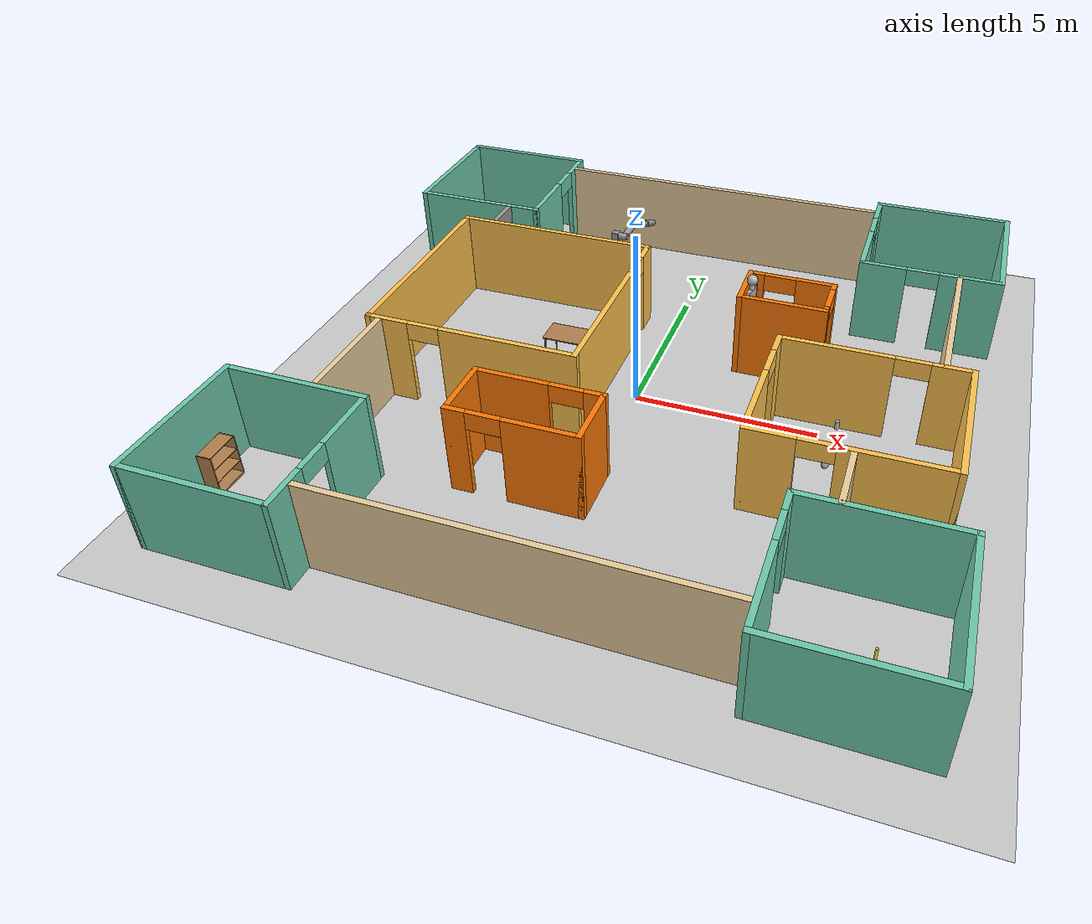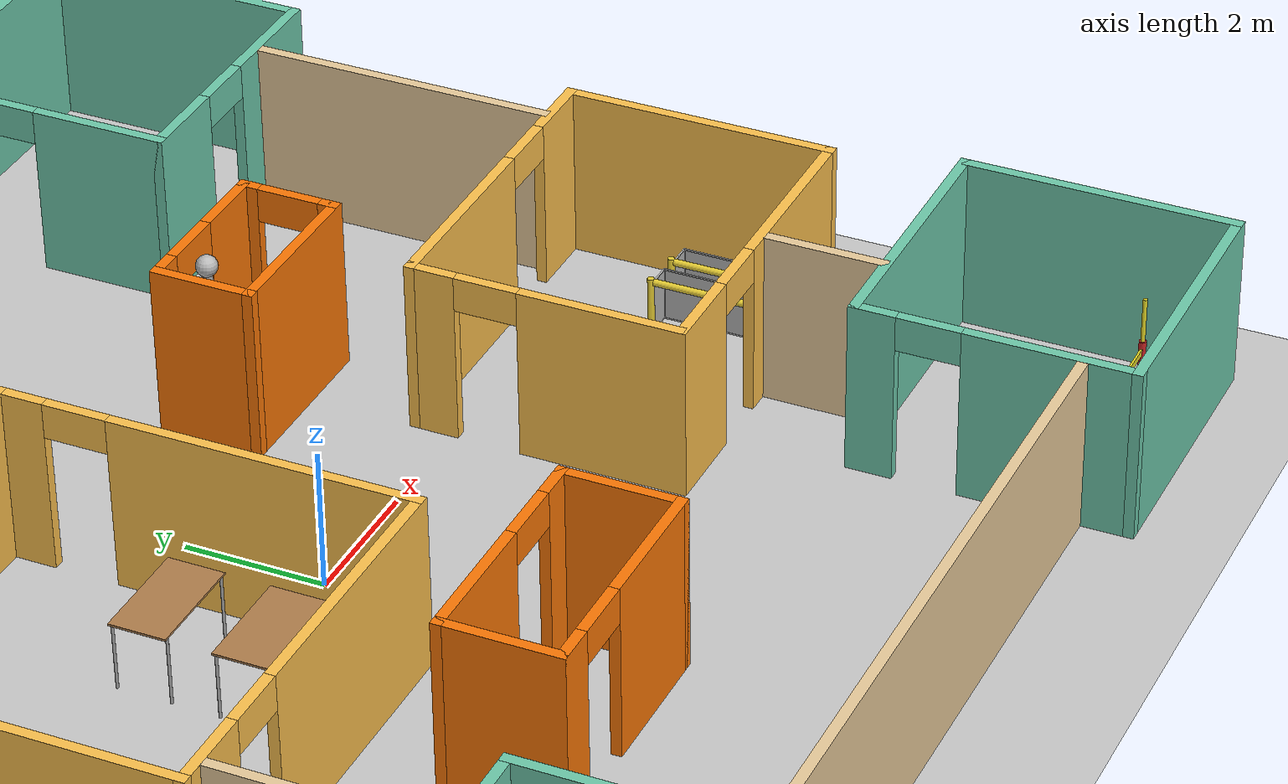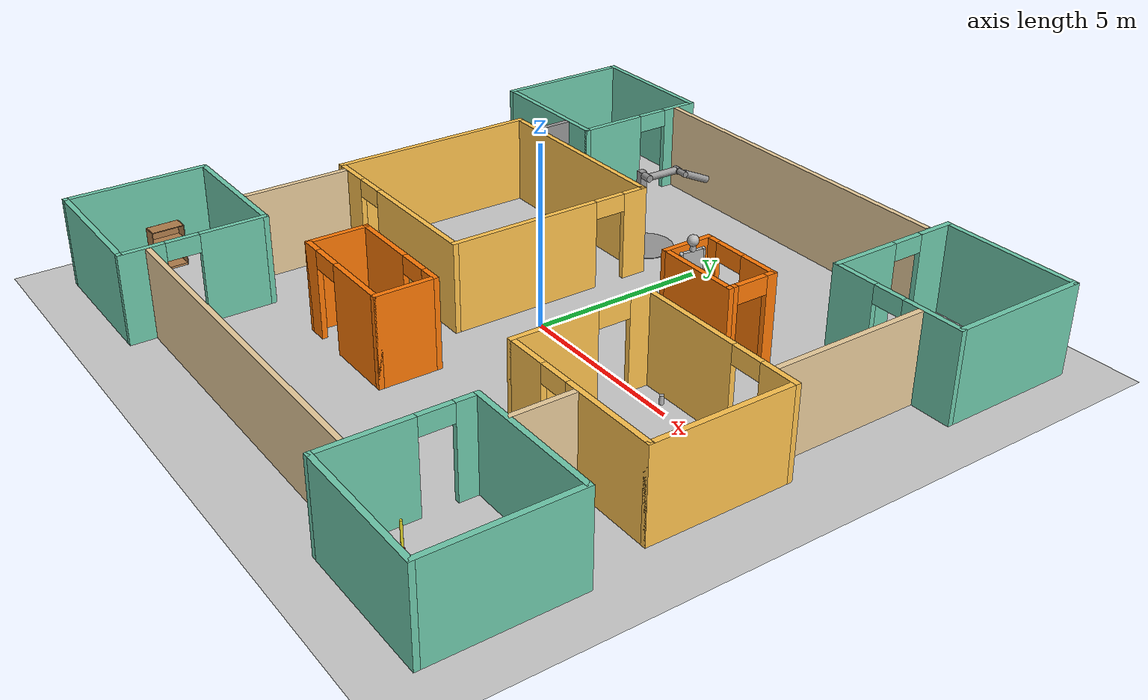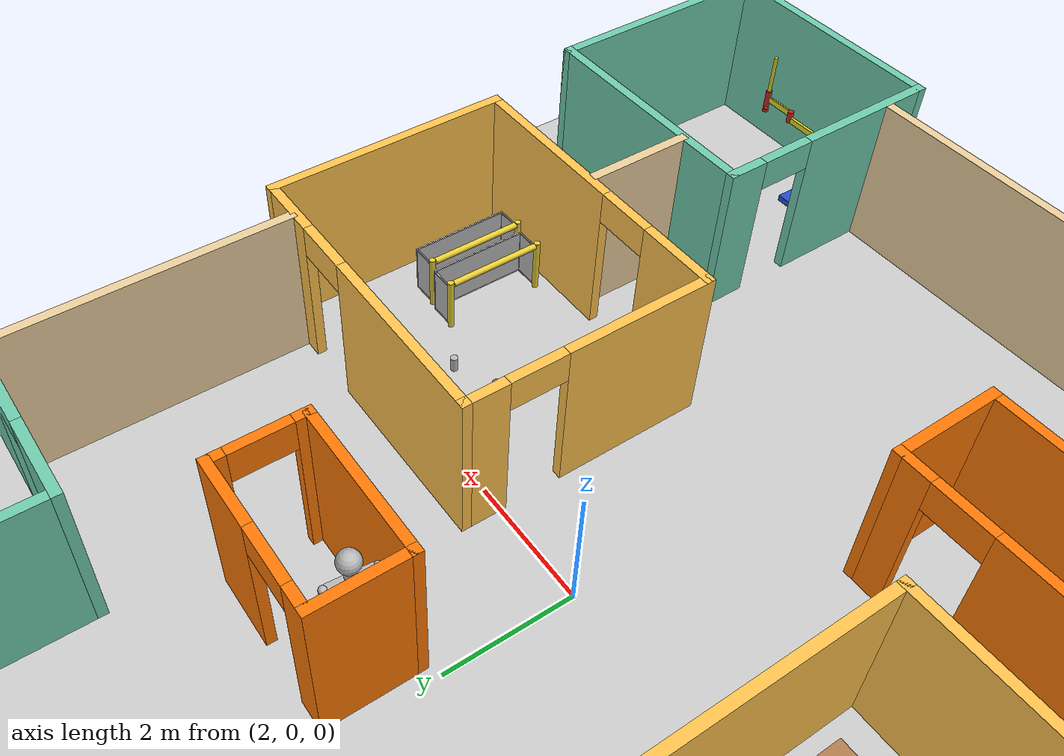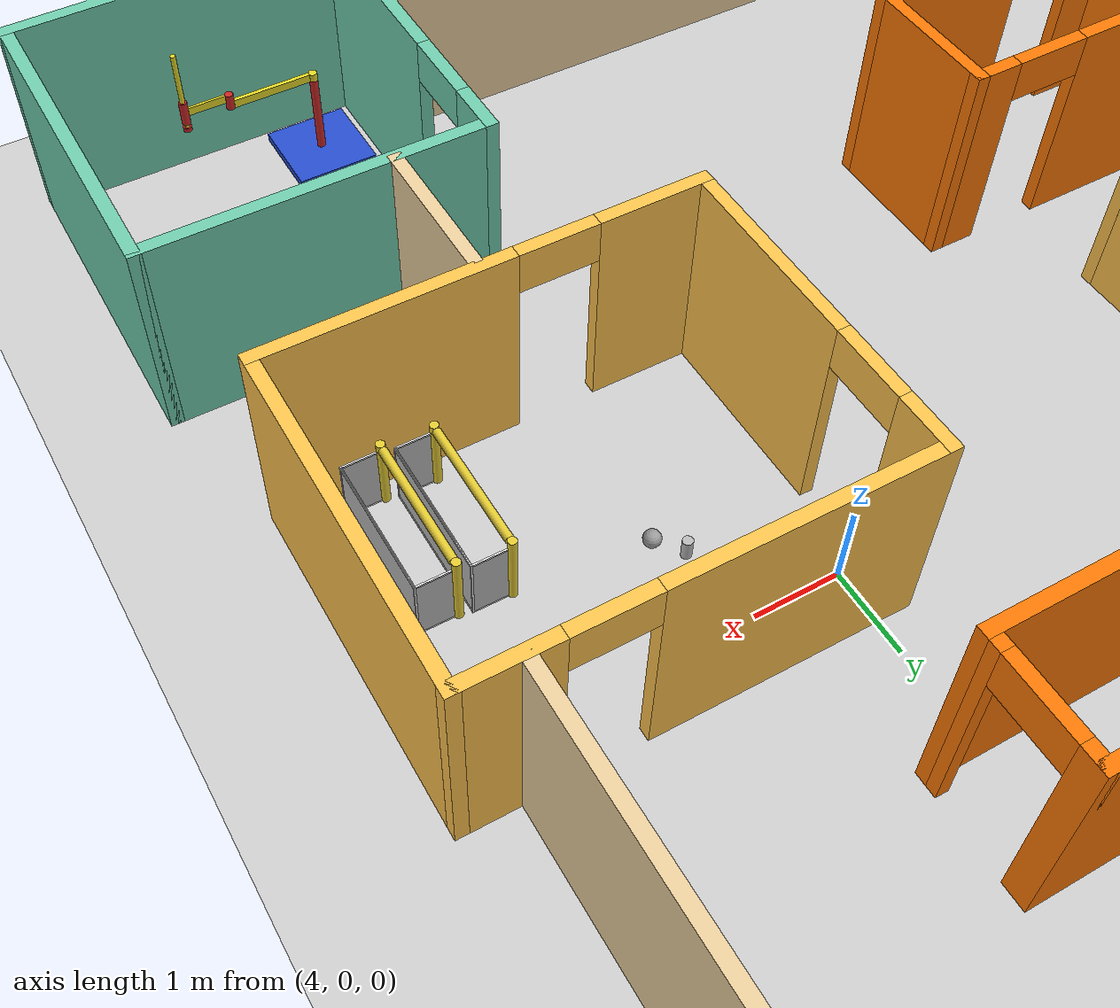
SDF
<sdf version="1.6">
 <world name="default">
  <plugin name="hello" filename="libhello.so"/>
  <light name="sun" type="directional">
   <pose>0 0 10 0 -0 0</pose>
   <diffuse>0.8 0.8 0.8 1</diffuse>
   <specular>0.2 0.2 0.2 1</specular>
   <attenuation>
    <range>1000</range>
    <constant>0.9</constant>
    <linear>0.01</linear>
    <quadratic>0.001</quadratic>
   </attenuation>
   <direction>-0.5 0.1 -0.9</direction>
  </light>
  <model name="ground_plane">
   <static>1</static>
   <link name="link">
    <collision name="collision">
     <geometry><plane><normal>0 0 1</normal><size>100 100</size></plane></geometry>
     <surface><friction><ode><mu>100</mu><mu2>50</mu2></ode></friction></surface>
    </collision>
    <visual name="visual">
     <cast_shadows>0</cast_shadows>
     <geometry><plane><normal>0 0 1</normal><size>100 100</size></plane></geometry>
     <material>
      <script><uri>file://media/materials/scripts/gazebo.material</uri><name>Gazebo/Grey</name></script>
     </material>
    </visual>
   </link>
  </model>
  <gravity>0 0 -9.8</gravity>
  <magnetic_field>6e-06 2.3e-05 -4.2e-05</magnetic_field>
  <atmosphere type="adiabatic"/>
  <physics name="default_physics" default="0" type="ode">
   <max_step_size>0.001</max_step_size>
   <real_time_factor>1</real_time_factor>
   <real_time_update_rate>1000</real_time_update_rate>
  </physics>
  <scene><ambient>0.4 0.4 0.4 1</ambient><background>0.7 0.7 0.7 1</background><shadows>1</shadows></scene>
  <spherical_coordinates>
   <surface_model>EARTH_WGS84</surface_model>
   <latitude_deg>0</latitude_deg>
   <longitude_deg>0</longitude_deg>
   <elevation>0</elevation>
   <heading_deg>0</heading_deg>
  </spherical_coordinates>
  <model name="building">
   <pose>0.04416 0.01107 0 0 -0 0</pose>
   <link name="Wall_100">
    <collision name="Wall_100_Collision">
     <geometry><box><size>2.5 0.15 2.5</size></box></geometry>
     <pose>0 0 1.25 0 -0 0</pose>
    </collision>
    <visual name="Wall_100_Visual">
     <pose>0 0 1.25 0 -0 0</pose>
     <geometry><box><size>2.5 0.15 2.5</size></box></geometry>
     <material>
      <script><uri>file://media/materials/scripts/gazebo.material</uri><name>Gazebo/Grey</name></script>
      <ambient>0.996078 0.47451 0.0196078 1</ambient>
     </material>
     <meta><layer>0</layer></meta>
    </visual>
    <pose>3.37853 2.13615 0 0 -0 3.14159</pose>
   </link>
   <link name="Wall_101">
    <collision name="Wall_101_Collision">
     <geometry><box><size>1.5 0.15 2.5</size></box></geometry>
     <pose>0 0 1.25 0 -0 0</pose>
    </collision>
    <visual name="Wall_101_Visual">
     <pose>0 0 1.25 0 -0 0</pose>
     <geometry><box><size>1.5 0.15 2.5</size></box></geometry>
     <material>
      <script><uri>file://media/materials/scripts/gazebo.material</uri><name>Gazebo/Grey</name></script>
      <ambient>0.996078 0.47451 0.0196078 1</ambient>
     </material>
     <meta><layer>0</layer></meta>
    </visual>
    <pose>2.20353 2.81115 0 0 -0 1.5708</pose>
   </link>
   <link name="Wall_103">
    <collision name="Wall_103_Collision">
     <geometry><box><size>1.75 0.15 2.5</size></box></geometry>
     <pose>0 0 1.25 0 -0 0</pose>
    </collision>
    <visual name="Wall_103_Visual">
     <pose>0 0 1.25 0 -0 0</pose>
     <geometry><box><size>1.75 0.15 2.5</size></box></geometry>
     <material>
      <script><uri>file://media/materials/scripts/gazebo.material</uri><name>Gazebo/Grey</name></script>
      <ambient>0.996078 0.47451 0.0196078 1</ambient>
     </material>
     <meta><layer>0</layer></meta>
    </visual>
    <pose>-3.11094 -4.01873 0 0 0 -1.5708</pose>
   </link>
   <link name="Wall_104">
    <pose>-1.43594 -4.81873 0 0 -0 0</pose>
    <visual name="Wall_104_Visual_0">
     <pose>-1.45465 0 1.25 0 -0 0</pose>
     <geometry><box><size>0.590693 0.15 2.5</size></box></geometry>
     <material>
      <script><uri>file://media/materials/scripts/gazebo.material</uri><name>Gazebo/Grey</name></script>
      <ambient>0.996078 0.47451 0.0196078 1</ambient>
     </material>
     <meta><layer>0</layer></meta>
    </visual>
    <collision name="Wall_104_Collision_0">
     <geometry><box><size>0.590693 0.15 2.5</size></box></geometry>
     <pose>-1.45465 0 1.25 0 -0 0</pose>
    </collision>
    <visual name="Wall_104_Visual_1">
     <pose>0.745346 0 1.25 0 -0 0</pose>
     <geometry><box><size>2.00931 0.15 2.5</size></box></geometry>
     <material>
      <script><uri>file://media/materials/scripts/gazebo.material</uri><name>Gazebo/Grey</name></script>
      <ambient>0.996078 0.47451 0.0196078 1</ambient>
     </material>
     <meta><layer>0</layer></meta>
    </visual>
    <collision name="Wall_104_Collision_1">
     <geometry><box><size>2.00931 0.15 2.5</size></box></geometry>
     <pose>0.745346 0 1.25 0 -0 0</pose>
    </collision>
    <visual name="Wall_104_Visual_2">
     <pose>-0.709307 0 2.25 0 -0 0</pose>
     <geometry><box><size>0.9 0.15 0.5</size></box></geometry>
     <material>
      <script><uri>file://media/materials/scripts/gazebo.material</uri><name>Gazebo/Grey</name></script>
      <ambient>0.996078 0.47451 0.0196078 1</ambient>
     </material>
     <meta><layer>0</layer></meta>
    </visual>
    <collision name="Wall_104_Collision_2">
     <geometry><box><size>0.9 0.15 0.5</size></box></geometry>
     <pose>-0.709307 0 2.25 0 -0 0</pose>
    </collision>
   </link>
   <link name="Wall_105">
    <collision name="Wall_105_Collision">
     <geometry><box><size>1.75 0.15 2.5</size></box></geometry>
     <pose>0 0 1.25 0 -0 0</pose>
    </collision>
    <visual name="Wall_105_Visual">
     <pose>0 0 1.25 0 -0 0</pose>
     <geometry><box><size>1.75 0.15 2.5</size></box></geometry>
     <material>
      <script><uri>file://media/materials/scripts/gazebo.material</uri><name>Gazebo/Grey</name></script>
      <ambient>0.996078 0.47451 0.0196078 1</ambient>
     </material>
     <meta><layer>0</layer></meta>
    </visual>
    <pose>0.239057 -4.01873 0 0 -0 1.5708</pose>
   </link>
   <link name="Wall_106">
    <pose>-1.43594 -3.21873 0 0 -0 3.14159</pose>
    <visual name="Wall_106_Visual_0">
     <pose>-1.46139 0 1.25 0 -0 0</pose>
     <geometry><box><size>0.577222 0.15 2.5</size></box></geometry>
     <material>
      <script><uri>file://media/materials/scripts/gazebo.material</uri><name>Gazebo/Grey</name></script>
      <ambient>0.996078 0.47451 0.0196078 1</ambient>
     </material>
     <meta><layer>0</layer></meta>
    </visual>
    <collision name="Wall_106_Collision_0">
     <geometry><box><size>0.577222 0.15 2.5</size></box></geometry>
     <pose>-1.46139 0 1.25 0 -0 0</pose>
    </collision>
    <visual name="Wall_106_Visual_1">
     <pose>0.738611 0 1.25 0 -0 0</pose>
     <geometry><box><size>2.02278 0.15 2.5</size></box></geometry>
     <material>
      <script><uri>file://media/materials/scripts/gazebo.material</uri><name>Gazebo/Grey</name></script>
      <ambient>0.996078 0.47451 0.0196078 1</ambient>
     </material>
     <meta><layer>0</layer></meta>
    </visual>
    <collision name="Wall_106_Collision_1">
     <geometry><box><size>2.02278 0.15 2.5</size></box></geometry>
     <pose>0.738611 0 1.25 0 -0 0</pose>
    </collision>
    <visual name="Wall_106_Visual_2">
     <pose>-0.722778 0 2.25 0 -0 0</pose>
     <geometry><box><size>0.9 0.15 0.5</size></box></geometry>
     <material>
      <script><uri>file://media/materials/scripts/gazebo.material</uri><name>Gazebo/Grey</name></script>
      <ambient>0.996078 0.47451 0.0196078 1</ambient>
     </material>
     <meta><layer>0</layer></meta>
    </visual>
    <collision name="Wall_106_Collision_2">
     <geometry><box><size>0.9 0.15 0.5</size></box></geometry>
     <pose>-0.722778 0 2.25 0 -0 0</pose>
    </collision>
   </link>
   <link name="Wall_108">
    <collision name="Wall_108_Collision">
     <geometry><box><size>3 0.15 2.5</size></box></geometry>
     <pose>0 0 1.25 0 -0 0</pose>
    </collision>
    <visual name="Wall_108_Visual">
     <pose>0 0 1.25 0 -0 0</pose>
     <geometry><box><size>3 0.15 2.5</size></box></geometry>
     <material>
      <script><uri>file://media/materials/scripts/gazebo.material</uri><name>Gazebo/Grey</name></script>
      <ambient>0.921569 0.807843 0.615686 1</ambient>
     </material>
     <meta><layer>0</layer></meta>
    </visual>
    <pose>-6.50973 -3.48506 0 0 0 -1.5708</pose>
   </link>
   <link name="Wall_114">
    <collision name="Wall_114_Collision">
     <geometry><box><size>4.5 0.15 2.5</size></box></geometry>
     <pose>0 0 1.25 0 -0 0</pose>
    </collision>
    <visual name="Wall_114_Visual">
     <pose>0 0 1.25 0 -0 0</pose>
     <geometry><box><size>4.5 0.15 2.5</size></box></geometry>
     <material>
      <script><uri>file://media/materials/scripts/gazebo.material</uri><name>Gazebo/Grey</name></script>
      <ambient>0.921569 0.807843 0.615686 1</ambient>
     </material>
     <meta><layer>0</layer></meta>
    </visual>
    <pose>7.81153 2.79707 0 0 0 -1.5708</pose>
   </link>
   <link name="Wall_116">
    <collision name="Wall_116_Collision">
     <geometry><box><size>10 0.15 2.5</size></box></geometry>
     <pose>0 0 1.25 0 -0 0</pose>
    </collision>
    <visual name="Wall_116_Visual">
     <pose>0 0 1.25 0 -0 0</pose>
     <geometry><box><size>10 0.15 2.5</size></box></geometry>
     <material>
      <script><uri>file://media/materials/scripts/gazebo.material</uri><name>Gazebo/Grey</name></script>
      <ambient>0.921569 0.807843 0.615686 1</ambient>
     </material>
     <meta><layer>0</layer></meta>
    </visual>
    <pose>0.006519 -8.20878 0 0 -0 0</pose>
   </link>
   <link name="Wall_118">
    <collision name="Wall_118_Collision">
     <geometry><box><size>1.75 0.15 2.5</size></box></geometry>
     <pose>0 0 1.25 0 -0 0</pose>
    </collision>
    <visual name="Wall_118_Visual">
     <pose>0 0 1.25 0 -0 0</pose>
     <geometry><box><size>1.75 0.15 2.5</size></box></geometry>
     <material>
      <script><uri>file://media/materials/scripts/gazebo.material</uri><name>Gazebo/Grey</name></script>
      <ambient>0.921569 0.807843 0.615686 1</ambient>
     </material>
     <meta><layer>0</layer></meta>
    </visual>
    <pose>6.15848 -4.23502 0 0 0 -1.5708</pose>
   </link>
   <link name="Wall_121">
    <collision name="Wall_121_Collision">
     <geometry><box><size>1 0.15 2.5</size></box></geometry>
     <pose>0 0 1.25 0 -0 0</pose>
    </collision>
    <visual name="Wall_121_Visual">
     <pose>0 0 1.25 0 -0 0</pose>
     <geometry><box><size>1 0.15 2.5</size></box></geometry>
     <material>
      <script><uri>file://media/materials/scripts/gazebo.material</uri><name>Gazebo/Grey</name></script>
      <ambient>1 1 1 1</ambient>
     </material>
     <meta><layer>0</layer></meta>
    </visual>
    <pose>-5.96902 4.51336 0 0 0 -1.5708</pose>
   </link>
   <link name="Wall_124">
    <collision name="Wall_124_Collision">
     <geometry><box><size>10 0.15 2.5</size></box></geometry>
     <pose>0 0 1.25 0 -0 0</pose>
    </collision>
    <visual name="Wall_124_Visual">
     <pose>0 0 1.25 0 -0 0</pose>
     <geometry><box><size>10 0.15 2.5</size></box></geometry>
     <material>
      <script><uri>file://media/materials/scripts/gazebo.material</uri><name>Gazebo/Grey</name></script>
      <ambient>0.921569 0.807843 0.615686 1</ambient>
     </material>
     <meta><layer>0</layer></meta>
    </visual>
    <pose>-0.024379 8.30625 0 0 -0 0</pose>
   </link>
   <link name="Wall_58">
    <collision name="Wall_58_Collision">
     <geometry><box><size>4 0.15 2.5</size></box></geometry>
     <pose>0 0 1.25 0 -0 0</pose>
    </collision>
    <visual name="Wall_58_Visual">
     <pose>0 0 1.25 0 -0 0</pose>
     <geometry><box><size>4 0.15 2.5</size></box></geometry>
     <material>
      <script><uri>file://media/materials/scripts/gazebo.material</uri><name>Gazebo/Grey</name></script>
      <ambient>0.435294 0.796078 0.67451 1</ambient>
     </material>
     <meta><layer>0</layer></meta>
    </visual>
    <pose>-7.00929 8.93364 0 0 -0 0</pose>
   </link>
   <link name="Wall_59">
    <pose>-5.08429 7.00864 0 0 0 -1.5708</pose>
    <visual name="Wall_59_Visual_0">
     <pose>-1.4441 0 1.25 0 -0 0</pose>
     <geometry><box><size>1.11179 0.15 2.5</size></box></geometry>
     <material>
      <script><uri>file://media/materials/scripts/gazebo.material</uri><name>Gazebo/Grey</name></script>
      <ambient>0.435294 0.796078 0.67451 1</ambient>
     </material>
     <meta><layer>0</layer></meta>
    </visual>
    <collision name="Wall_59_Collision_0">
     <geometry><box><size>1.11179 0.15 2.5</size></box></geometry>
     <pose>-1.4441 0 1.25 0 -0 0</pose>
    </collision>
    <visual name="Wall_59_Visual_1">
     <pose>1.0059 0 1.25 0 -0 0</pose>
     <geometry><box><size>1.98821 0.15 2.5</size></box></geometry>
     <material>
      <script><uri>file://media/materials/scripts/gazebo.material</uri><name>Gazebo/Grey</name></script>
      <ambient>0.435294 0.796078 0.67451 1</ambient>
     </material>
     <meta><layer>0</layer></meta>
    </visual>
    <collision name="Wall_59_Collision_1">
     <geometry><box><size>1.98821 0.15 2.5</size></box></geometry>
     <pose>1.0059 0 1.25 0 -0 0</pose>
    </collision>
    <visual name="Wall_59_Visual_2">
     <pose>-0.438207 0 2.25 0 -0 0</pose>
     <geometry><box><size>0.9 0.15 0.5</size></box></geometry>
     <material>
      <script><uri>file://media/materials/scripts/gazebo.material</uri><name>Gazebo/Grey</name></script>
      <ambient>0.435294 0.796078 0.67451 1</ambient>
     </material>
     <meta><layer>0</layer></meta>
    </visual>
    <collision name="Wall_59_Collision_2">
     <geometry><box><size>0.9 0.15 0.5</size></box></geometry>
     <pose>-0.438207 0 2.25 0 -0 0</pose>
    </collision>
   </link>
   <link name="Wall_60">
    <collision name="Wall_60_Collision">
     <geometry><box><size>4 0.15 2.5</size></box></geometry>
     <pose>0 0 1.25 0 -0 0</pose>
    </collision>
    <visual name="Wall_60_Visual">
     <pose>0 0 1.25 0 -0 0</pose>
     <geometry><box><size>4 0.15 2.5</size></box></geometry>
     <material>
      <script><uri>file://media/materials/scripts/gazebo.material</uri><name>Gazebo/Grey</name></script>
      <ambient>0.435294 0.796078 0.67451 1</ambient>
     </material>
     <meta><layer>0</layer></meta>
    </visual>
    <pose>-7.00929 5.08364 0 0 -0 3.14159</pose>
   </link>
   <link name="Wall_61">
    <collision name="Wall_61_Collision">
     <geometry><box><size>4 0.15 2.5</size></box></geometry>
     <pose>0 0 1.25 0 -0 0</pose>
    </collision>
    <visual name="Wall_61_Visual">
     <pose>0 0 1.25 0 -0 0</pose>
     <geometry><box><size>4 0.15 2.5</size></box></geometry>
     <material>
      <script><uri>file://media/materials/scripts/gazebo.material</uri><name>Gazebo/Grey</name></script>
      <ambient>0.435294 0.796078 0.67451 1</ambient>
     </material>
     <meta><layer>0</layer></meta>
    </visual>
    <pose>-8.93429 7.00864 0 0 -0 1.5708</pose>
   </link>
   <link name="Wall_63">
    <collision name="Wall_63_Collision">
     <geometry><box><size>4 0.15 2.5</size></box></geometry>
     <pose>0 0 1.25 0 -0 0</pose>
    </collision>
    <visual name="Wall_63_Visual">
     <pose>0 0 1.25 0 -0 0</pose>
     <geometry><box><size>4 0.15 2.5</size></box></geometry>
     <material>
      <script><uri>file://media/materials/scripts/gazebo.material</uri><name>Gazebo/Grey</name></script>
      <ambient>0.435294 0.796078 0.67451 1</ambient>
     </material>
     <meta><layer>0</layer></meta>
    </visual>
    <pose>8.93429 6.99136 0 0 0 -1.5708</pose>
   </link>
   <link name="Wall_64">
    <pose>7.00929 5.06635 0 0 -0 3.14159</pose>
    <visual name="Wall_64_Visual_0">
     <pose>-1.11962 0 1.25 0 -0 0</pose>
     <geometry><box><size>1.76077 0.15 2.5</size></box></geometry>
     <material>
      <script><uri>file://media/materials/scripts/gazebo.material</uri><name>Gazebo/Grey</name></script>
      <ambient>0.435294 0.796078 0.67451 1</ambient>
     </material>
     <meta><layer>0</layer></meta>
    </visual>
    <collision name="Wall_64_Collision_0">
     <geometry><box><size>1.76077 0.15 2.5</size></box></geometry>
     <pose>-1.11962 0 1.25 0 -0 0</pose>
    </collision>
    <visual name="Wall_64_Visual_1">
     <pose>1.33038 0 1.25 0 -0 0</pose>
     <geometry><box><size>1.33923 0.15 2.5</size></box></geometry>
     <material>
      <script><uri>file://media/materials/scripts/gazebo.material</uri><name>Gazebo/Grey</name></script>
      <ambient>0.435294 0.796078 0.67451 1</ambient>
     </material>
     <meta><layer>0</layer></meta>
    </visual>
    <collision name="Wall_64_Collision_1">
     <geometry><box><size>1.33923 0.15 2.5</size></box></geometry>
     <pose>1.33038 0 1.25 0 -0 0</pose>
    </collision>
    <visual name="Wall_64_Visual_2">
     <pose>0.210767 0 2.25 0 -0 0</pose>
     <geometry><box><size>0.9 0.15 0.5</size></box></geometry>
     <material>
      <script><uri>file://media/materials/scripts/gazebo.material</uri><name>Gazebo/Grey</name></script>
      <ambient>0.435294 0.796078 0.67451 1</ambient>
     </material>
     <meta><layer>0</layer></meta>
    </visual>
    <collision name="Wall_64_Collision_2">
     <geometry><box><size>0.9 0.15 0.5</size></box></geometry>
     <pose>0.210767 0 2.25 0 -0 0</pose>
    </collision>
   </link>
   <link name="Wall_65">
    <pose>5.08429 6.99136 0 0 -0 1.5708</pose>
    <visual name="Wall_65_Visual_0">
     <pose>-0.997252 0 1.25 0 -0 0</pose>
     <geometry><box><size>2.0055 0.15 2.5</size></box></geometry>
     <material>
      <script><uri>file://media/materials/scripts/gazebo.material</uri><name>Gazebo/Grey</name></script>
      <ambient>0.435294 0.796078 0.67451 1</ambient>
     </material>
     <meta><layer>0</layer></meta>
    </visual>
    <collision name="Wall_65_Collision_0">
     <geometry><box><size>2.0055 0.15 2.5</size></box></geometry>
     <pose>-0.997252 0 1.25 0 -0 0</pose>
    </collision>
    <visual name="Wall_65_Visual_1">
     <pose>1.45275 0 1.25 0 -0 0</pose>
     <geometry><box><size>1.0945 0.15 2.5</size></box></geometry>
     <material>
      <script><uri>file://media/materials/scripts/gazebo.material</uri><name>Gazebo/Grey</name></script>
      <ambient>0.435294 0.796078 0.67451 1</ambient>
     </material>
     <meta><layer>0</layer></meta>
    </visual>
    <collision name="Wall_65_Collision_1">
     <geometry><box><size>1.0945 0.15 2.5</size></box></geometry>
     <pose>1.45275 0 1.25 0 -0 0</pose>
    </collision>
    <visual name="Wall_65_Visual_2">
     <pose>0.455496 0 2.25 0 -0 0</pose>
     <geometry><box><size>0.9 0.15 0.5</size></box></geometry>
     <material>
      <script><uri>file://media/materials/scripts/gazebo.material</uri><name>Gazebo/Grey</name></script>
      <ambient>0.435294 0.796078 0.67451 1</ambient>
     </material>
     <meta><layer>0</layer></meta>
    </visual>
    <collision name="Wall_65_Collision_2">
     <geometry><box><size>0.9 0.15 0.5</size></box></geometry>
     <pose>0.455496 0 2.25 0 -0 0</pose>
    </collision>
   </link>
   <link name="Wall_66">
    <collision name="Wall_66_Collision">
     <geometry><box><size>4 0.15 2.5</size></box></geometry>
     <pose>0 0 1.25 0 -0 0</pose>
    </collision>
    <visual name="Wall_66_Visual">
     <pose>0 0 1.25 0 -0 0</pose>
     <geometry><box><size>4 0.15 2.5</size></box></geometry>
     <material>
      <script><uri>file://media/materials/scripts/gazebo.material</uri><name>Gazebo/Grey</name></script>
      <ambient>0.435294 0.796078 0.67451 1</ambient>
     </material>
     <meta><layer>0</layer></meta>
    </visual>
    <pose>7.00929 8.91635 0 0 -0 0</pose>
   </link>
   <link name="Wall_71">
    <collision name="Wall_71_Collision">
     <geometry><box><size>4 0.15 2.5</size></box></geometry>
     <pose>0 0 1.25 0 -0 0</pose>
    </collision>
    <visual name="Wall_71_Visual">
     <pose>0 0 1.25 0 -0 0</pose>
     <geometry><box><size>4 0.15 2.5</size></box></geometry>
     <material>
      <script><uri>file://media/materials/scripts/gazebo.material</uri><name>Gazebo/Grey</name></script>
      <ambient>0.435294 0.796078 0.67451 1</ambient>
     </material>
     <meta><layer>0</layer></meta>
    </visual>
    <pose>7.00929 -8.93364 0 0 -0 3.14159</pose>
   </link>
   <link name="Wall_72">
    <pose>5.08429 -7.00864 0 0 -0 1.5708</pose>
    <visual name="Wall_72_Visual_0">
     <pose>-0.779391 0 1.25 0 -0 0</pose>
     <geometry><box><size>2.44122 0.15 2.5</size></box></geometry>
     <material>
      <script><uri>file://media/materials/scripts/gazebo.material</uri><name>Gazebo/Grey</name></script>
      <ambient>0.435294 0.796078 0.67451 1</ambient>
     </material>
     <meta><layer>0</layer></meta>
    </visual>
    <collision name="Wall_72_Collision_0">
     <geometry><box><size>2.44122 0.15 2.5</size></box></geometry>
     <pose>-0.779391 0 1.25 0 -0 0</pose>
    </collision>
    <visual name="Wall_72_Visual_1">
     <pose>1.67061 0 1.25 0 -0 0</pose>
     <geometry><box><size>0.658782 0.15 2.5</size></box></geometry>
     <material>
      <script><uri>file://media/materials/scripts/gazebo.material</uri><name>Gazebo/Grey</name></script>
      <ambient>0.435294 0.796078 0.67451 1</ambient>
     </material>
     <meta><layer>0</layer></meta>
    </visual>
    <collision name="Wall_72_Collision_1">
     <geometry><box><size>0.658782 0.15 2.5</size></box></geometry>
     <pose>1.67061 0 1.25 0 -0 0</pose>
    </collision>
    <visual name="Wall_72_Visual_2">
     <pose>0.891218 0 2.25 0 -0 0</pose>
     <geometry><box><size>0.9 0.15 0.5</size></box></geometry>
     <material>
      <script><uri>file://media/materials/scripts/gazebo.material</uri><name>Gazebo/Grey</name></script>
      <ambient>0.435294 0.796078 0.67451 1</ambient>
     </material>
     <meta><layer>0</layer></meta>
    </visual>
    <collision name="Wall_72_Collision_2">
     <geometry><box><size>0.9 0.15 0.5</size></box></geometry>
     <pose>0.891218 0 2.25 0 -0 0</pose>
    </collision>
   </link>
   <link name="Wall_73">
    <collision name="Wall_73_Collision">
     <geometry><box><size>4 0.15 2.5</size></box></geometry>
     <pose>0 0 1.25 0 -0 0</pose>
    </collision>
    <visual name="Wall_73_Visual">
     <pose>0 0 1.25 0 -0 0</pose>
     <geometry><box><size>4 0.15 2.5</size></box></geometry>
     <material>
      <script><uri>file://media/materials/scripts/gazebo.material</uri><name>Gazebo/Grey</name></script>
      <ambient>0.435294 0.796078 0.67451 1</ambient>
     </material>
     <meta><layer>0</layer></meta>
    </visual>
    <pose>7.00929 -5.08364 0 0 -0 0</pose>
   </link>
   <link name="Wall_74">
    <collision name="Wall_74_Collision">
     <geometry><box><size>4 0.15 2.5</size></box></geometry>
     <pose>0 0 1.25 0 -0 0</pose>
    </collision>
    <visual name="Wall_74_Visual">
     <pose>0 0 1.25 0 -0 0</pose>
     <geometry><box><size>4 0.15 2.5</size></box></geometry>
     <material>
      <script><uri>file://media/materials/scripts/gazebo.material</uri><name>Gazebo/Grey</name></script>
      <ambient>0.435294 0.796078 0.67451 1</ambient>
     </material>
     <meta><layer>0</layer></meta>
    </visual>
    <pose>8.93429 -7.00864 0 0 0 -1.5708</pose>
   </link>
   <link name="Wall_76">
    <collision name="Wall_76_Collision">
     <geometry><box><size>4 0.15 2.5</size></box></geometry>
     <pose>0 0 1.25 0 -0 0</pose>
    </collision>
    <visual name="Wall_76_Visual">
     <pose>0 0 1.25 0 -0 0</pose>
     <geometry><box><size>4 0.15 2.5</size></box></geometry>
     <material>
      <script><uri>file://media/materials/scripts/gazebo.material</uri><name>Gazebo/Grey</name></script>
      <ambient>0.435294 0.796078 0.67451 1</ambient>
     </material>
     <meta><layer>0</layer></meta>
    </visual>
    <pose>-7.00929 -8.91636 0 0 -0 0</pose>
   </link>
   <link name="Wall_77">
    <pose>-5.08429 -6.99136 0 0 -0 1.5708</pose>
    <visual name="Wall_77_Visual_0">
     <pose>-1.38249 0 1.25 0 -0 0</pose>
     <geometry><box><size>1.23503 0.15 2.5</size></box></geometry>
     <material>
      <script><uri>file://media/materials/scripts/gazebo.material</uri><name>Gazebo/Grey</name></script>
      <ambient>0.435294 0.796078 0.67451 1</ambient>
     </material>
     <meta><layer>0</layer></meta>
    </visual>
    <collision name="Wall_77_Collision_0">
     <geometry><box><size>1.23503 0.15 2.5</size></box></geometry>
     <pose>-1.38249 0 1.25 0 -0 0</pose>
    </collision>
    <visual name="Wall_77_Visual_1">
     <pose>1.06751 0 1.25 0 -0 0</pose>
     <geometry><box><size>1.86497 0.15 2.5</size></box></geometry>
     <material>
      <script><uri>file://media/materials/scripts/gazebo.material</uri><name>Gazebo/Grey</name></script>
      <ambient>0.435294 0.796078 0.67451 1</ambient>
     </material>
     <meta><layer>0</layer></meta>
    </visual>
    <collision name="Wall_77_Collision_1">
     <geometry><box><size>1.86497 0.15 2.5</size></box></geometry>
     <pose>1.06751 0 1.25 0 -0 0</pose>
    </collision>
    <visual name="Wall_77_Visual_2">
     <pose>-0.314972 0 2.25 0 -0 0</pose>
     <geometry><box><size>0.9 0.15 0.5</size></box></geometry>
     <material>
      <script><uri>file://media/materials/scripts/gazebo.material</uri><name>Gazebo/Grey</name></script>
      <ambient>0.435294 0.796078 0.67451 1</ambient>
     </material>
     <meta><layer>0</layer></meta>
    </visual>
    <collision name="Wall_77_Collision_2">
     <geometry><box><size>0.9 0.15 0.5</size></box></geometry>
     <pose>-0.314972 0 2.25 0 -0 0</pose>
    </collision>
   </link>
   <link name="Wall_78">
    <collision name="Wall_78_Collision">
     <geometry><box><size>4 0.15 2.5</size></box></geometry>
     <pose>0 0 1.25 0 -0 0</pose>
    </collision>
    <visual name="Wall_78_Visual">
     <pose>0 0 1.25 0 -0 0</pose>
     <geometry><box><size>4 0.15 2.5</size></box></geometry>
     <material>
      <script><uri>file://media/materials/scripts/gazebo.material</uri><name>Gazebo/Grey</name></script>
      <ambient>0.435294 0.796078 0.67451 1</ambient>
     </material>
     <meta><layer>0</layer></meta>
    </visual>
    <pose>-7.00929 -5.06636 0 0 -0 3.14159</pose>
   </link>
   <link name="Wall_79">
    <collision name="Wall_79_Collision">
     <geometry><box><size>4 0.15 2.5</size></box></geometry>
     <pose>0 0 1.25 0 -0 0</pose>
    </collision>
    <visual name="Wall_79_Visual">
     <pose>0 0 1.25 0 -0 0</pose>
     <geometry><box><size>4 0.15 2.5</size></box></geometry>
     <material>
      <script><uri>file://media/materials/scripts/gazebo.material</uri><name>Gazebo/Grey</name></script>
      <ambient>0.435294 0.796078 0.67451 1</ambient>
     </material>
     <meta><layer>0</layer></meta>
    </visual>
    <pose>-8.93429 -6.99136 0 0 0 -1.5708</pose>
   </link>
   <link name="Wall_84">
    <collision name="Wall_84_Collision">
     <geometry><box><size>6 0.15 2.5</size></box></geometry>
     <pose>0 0 1.25 0 -0 0</pose>
    </collision>
    <visual name="Wall_84_Visual">
     <pose>0 0 1.25 0 -0 0</pose>
     <geometry><box><size>6 0.15 2.5</size></box></geometry>
     <material>
      <script><uri>file://media/materials/scripts/gazebo.material</uri><name>Gazebo/Grey</name></script>
      <ambient>1 0.764706 0.305882 1</ambient>
     </material>
     <meta><layer>0</layer></meta>
    </visual>
    <pose>-3.94006 3.93417 0 0 -0 0</pose>
   </link>
   <link name="Wall_85">
    <pose>-1.01506 1.00917 0 0 0 -1.5708</pose>
    <visual name="Wall_85_Visual_0">
     <pose>-2.63359 0 1.25 0 -0 0</pose>
     <geometry><box><size>0.732823 0.15 2.5</size></box></geometry>
     <material>
      <script><uri>file://media/materials/scripts/gazebo.material</uri><name>Gazebo/Grey</name></script>
      <ambient>1 0.764706 0.305882 1</ambient>
     </material>
     <meta><layer>0</layer></meta>
    </visual>
    <collision name="Wall_85_Collision_0">
     <geometry><box><size>0.732823 0.15 2.5</size></box></geometry>
     <pose>-2.63359 0 1.25 0 -0 0</pose>
    </collision>
    <visual name="Wall_85_Visual_1">
     <pose>0.816412 0 1.25 0 -0 0</pose>
     <geometry><box><size>4.36718 0.15 2.5</size></box></geometry>
     <material>
      <script><uri>file://media/materials/scripts/gazebo.material</uri><name>Gazebo/Grey</name></script>
      <ambient>1 0.764706 0.305882 1</ambient>
     </material>
     <meta><layer>0</layer></meta>
    </visual>
    <collision name="Wall_85_Collision_1">
     <geometry><box><size>4.36718 0.15 2.5</size></box></geometry>
     <pose>0.816412 0 1.25 0 -0 0</pose>
    </collision>
    <visual name="Wall_85_Visual_2">
     <pose>-1.81718 0 2.25 0 -0 0</pose>
     <geometry><box><size>0.9 0.15 0.5</size></box></geometry>
     <material>
      <script><uri>file://media/materials/scripts/gazebo.material</uri><name>Gazebo/Grey</name></script>
      <ambient>1 0.764706 0.305882 1</ambient>
     </material>
     <meta><layer>0</layer></meta>
    </visual>
    <collision name="Wall_85_Collision_2">
     <geometry><box><size>0.9 0.15 0.5</size></box></geometry>
     <pose>-1.81718 0 2.25 0 -0 0</pose>
    </collision>
   </link>
   <link name="Wall_86">
    <pose>-3.94006 -1.91583 0 0 -0 3.14159</pose>
    <visual name="Wall_86_Visual_0">
     <pose>-1.06873 0 1.25 0 -0 0</pose>
     <geometry><box><size>3.86254 0.15 2.5</size></box></geometry>
     <material>
      <script><uri>file://media/materials/scripts/gazebo.material</uri><name>Gazebo/Grey</name></script>
      <ambient>1 0.764706 0.305882 1</ambient>
     </material>
     <meta><layer>0</layer></meta>
    </visual>
    <collision name="Wall_86_Collision_0">
     <geometry><box><size>3.86254 0.15 2.5</size></box></geometry>
     <pose>-1.06873 0 1.25 0 -0 0</pose>
    </collision>
    <visual name="Wall_86_Visual_1">
     <pose>2.38127 0 1.25 0 -0 0</pose>
     <geometry><box><size>1.23746 0.15 2.5</size></box></geometry>
     <material>
      <script><uri>file://media/materials/scripts/gazebo.material</uri><name>Gazebo/Grey</name></script>
      <ambient>1 0.764706 0.305882 1</ambient>
     </material>
     <meta><layer>0</layer></meta>
    </visual>
    <collision name="Wall_86_Collision_1">
     <geometry><box><size>1.23746 0.15 2.5</size></box></geometry>
     <pose>2.38127 0 1.25 0 -0 0</pose>
    </collision>
    <visual name="Wall_86_Visual_2">
     <pose>1.31254 0 2.25 0 -0 0</pose>
     <geometry><box><size>0.9 0.15 0.5</size></box></geometry>
     <material>
      <script><uri>file://media/materials/scripts/gazebo.material</uri><name>Gazebo/Grey</name></script>
      <ambient>1 0.764706 0.305882 1</ambient>
     </material>
     <meta><layer>0</layer></meta>
    </visual>
    <collision name="Wall_86_Collision_2">
     <geometry><box><size>0.9 0.15 0.5</size></box></geometry>
     <pose>1.31254 0 2.25 0 -0 0</pose>
    </collision>
   </link>
   <link name="Wall_87">
    <collision name="Wall_87_Collision">
     <geometry><box><size>6 0.15 2.5</size></box></geometry>
     <pose>0 0 1.25 0 -0 0</pose>
    </collision>
    <visual name="Wall_87_Visual">
     <pose>0 0 1.25 0 -0 0</pose>
     <geometry><box><size>6 0.15 2.5</size></box></geometry>
     <material>
      <script><uri>file://media/materials/scripts/gazebo.material</uri><name>Gazebo/Grey</name></script>
      <ambient>1 0.764706 0.305882 1</ambient>
     </material>
     <meta><layer>0</layer></meta>
    </visual>
    <pose>-6.86506 1.00917 0 0 -0 1.5708</pose>
   </link>
   <link name="Wall_89">
    <collision name="Wall_89_Collision">
     <geometry><box><size>4 0.15 2.5</size></box></geometry>
     <pose>0 0 1.25 0 -0 0</pose>
    </collision>
    <visual name="Wall_89_Visual">
     <pose>0 0 1.25 0 -0 0</pose>
     <geometry><box><size>4 0.15 2.5</size></box></geometry>
     <material>
      <script><uri>file://media/materials/scripts/gazebo.material</uri><name>Gazebo/Grey</name></script>
      <ambient>1 0.764706 0.305882 1</ambient>
     </material>
     <meta><layer>0</layer></meta>
    </visual>
    <pose>8.49129 -1.38643 0 0 -0 1.5708</pose>
   </link>
   <link name="Wall_90">
    <pose>6.06629 0.538572 0 0 -0 3.14159</pose>
    <visual name="Wall_90_Visual_0">
     <pose>-1.9492 0 1.25 0 -0 0</pose>
     <geometry><box><size>1.1016 0.15 2.5</size></box></geometry>
     <material>
      <script><uri>file://media/materials/scripts/gazebo.material</uri><name>Gazebo/Grey</name></script>
      <ambient>1 0.764706 0.305882 1</ambient>
     </material>
     <meta><layer>0</layer></meta>
    </visual>
    <collision name="Wall_90_Collision_0">
     <geometry><box><size>1.1016 0.15 2.5</size></box></geometry>
     <pose>-1.9492 0 1.25 0 -0 0</pose>
    </collision>
    <visual name="Wall_90_Visual_1">
     <pose>1.0008 0 1.25 0 -0 0</pose>
     <geometry><box><size>2.9984 0.15 2.5</size></box></geometry>
     <material>
      <script><uri>file://media/materials/scripts/gazebo.material</uri><name>Gazebo/Grey</name></script>
      <ambient>1 0.764706 0.305882 1</ambient>
     </material>
     <meta><layer>0</layer></meta>
    </visual>
    <collision name="Wall_90_Collision_1">
     <geometry><box><size>2.9984 0.15 2.5</size></box></geometry>
     <pose>1.0008 0 1.25 0 -0 0</pose>
    </collision>
    <visual name="Wall_90_Visual_2">
     <pose>-0.948401 0 2.25 0 -0 0</pose>
     <geometry><box><size>0.9 0.15 0.5</size></box></geometry>
     <material>
      <script><uri>file://media/materials/scripts/gazebo.material</uri><name>Gazebo/Grey</name></script>
      <ambient>1 0.764706 0.305882 1</ambient>
     </material>
     <meta><layer>0</layer></meta>
    </visual>
    <collision name="Wall_90_Collision_2">
     <geometry><box><size>0.9 0.15 0.5</size></box></geometry>
     <pose>-0.948401 0 2.25 0 -0 0</pose>
    </collision>
   </link>
   <link name="Wall_91">
    <pose>3.64129 -1.38643 0 0 0 -1.5708</pose>
    <visual name="Wall_91_Visual_0">
     <pose>-1.64261 0 1.25 0 -0 0</pose>
     <geometry><box><size>0.714781 0.15 2.5</size></box></geometry>
     <material>
      <script><uri>file://media/materials/scripts/gazebo.material</uri><name>Gazebo/Grey</name></script>
      <ambient>1 0.764706 0.305882 1</ambient>
     </material>
     <meta><layer>0</layer></meta>
    </visual>
    <collision name="Wall_91_Collision_0">
     <geometry><box><size>0.714781 0.15 2.5</size></box></geometry>
     <pose>-1.64261 0 1.25 0 -0 0</pose>
    </collision>
    <visual name="Wall_91_Visual_1">
     <pose>0.80739 0 1.25 0 -0 0</pose>
     <geometry><box><size>2.38522 0.15 2.5</size></box></geometry>
     <material>
      <script><uri>file://media/materials/scripts/gazebo.material</uri><name>Gazebo/Grey</name></script>
      <ambient>1 0.764706 0.305882 1</ambient>
     </material>
     <meta><layer>0</layer></meta>
    </visual>
    <collision name="Wall_91_Collision_1">
     <geometry><box><size>2.38522 0.15 2.5</size></box></geometry>
     <pose>0.80739 0 1.25 0 -0 0</pose>
    </collision>
    <visual name="Wall_91_Visual_2">
     <pose>-0.835219 0 2.25 0 -0 0</pose>
     <geometry><box><size>0.9 0.15 0.5</size></box></geometry>
     <material>
      <script><uri>file://media/materials/scripts/gazebo.material</uri><name>Gazebo/Grey</name></script>
      <ambient>1 0.764706 0.305882 1</ambient>
     </material>
     <meta><layer>0</layer></meta>
    </visual>
    <collision name="Wall_91_Collision_2">
     <geometry><box><size>0.9 0.15 0.5</size></box></geometry>
     <pose>-0.835219 0 2.25 0 -0 0</pose>
    </collision>
   </link>
   <link name="Wall_92">
    <pose>6.06629 -3.31143 0 0 -0 0</pose>
    <visual name="Wall_92_Visual_0">
     <pose>-1.85194 0 1.25 0 -0 0</pose>
     <geometry><box><size>1.29611 0.15 2.5</size></box></geometry>
     <material>
      <script><uri>file://media/materials/scripts/gazebo.material</uri><name>Gazebo/Grey</name></script>
      <ambient>1 0.764706 0.305882 1</ambient>
     </material>
     <meta><layer>0</layer></meta>
    </visual>
    <collision name="Wall_92_Collision_0">
     <geometry><box><size>1.29611 0.15 2.5</size></box></geometry>
     <pose>-1.85194 0 1.25 0 -0 0</pose>
    </collision>
    <visual name="Wall_92_Visual_1">
     <pose>1.09806 0 1.25 0 -0 0</pose>
     <geometry><box><size>2.80389 0.15 2.5</size></box></geometry>
     <material>
      <script><uri>file://media/materials/scripts/gazebo.material</uri><name>Gazebo/Grey</name></script>
      <ambient>1 0.764706 0.305882 1</ambient>
     </material>
     <meta><layer>0</layer></meta>
    </visual>
    <collision name="Wall_92_Collision_1">
     <geometry><box><size>2.80389 0.15 2.5</size></box></geometry>
     <pose>1.09806 0 1.25 0 -0 0</pose>
    </collision>
    <visual name="Wall_92_Visual_2">
     <pose>-0.753889 0 2.25 0 -0 0</pose>
     <geometry><box><size>0.9 0.15 0.5</size></box></geometry>
     <material>
      <script><uri>file://media/materials/scripts/gazebo.material</uri><name>Gazebo/Grey</name></script>
      <ambient>1 0.764706 0.305882 1</ambient>
     </material>
     <meta><layer>0</layer></meta>
    </visual>
    <collision name="Wall_92_Collision_2">
     <geometry><box><size>0.9 0.15 0.5</size></box></geometry>
     <pose>-0.753889 0 2.25 0 -0 0</pose>
    </collision>
   </link>
   <link name="Wall_98">
    <pose>3.37853 3.48615 0 0 -0 0</pose>
    <visual name="Wall_98_Visual_0">
     <pose>-1.01792 0 1.25 0 -0 0</pose>
     <geometry><box><size>0.464152 0.15 2.5</size></box></geometry>
     <material>
      <script><uri>file://media/materials/scripts/gazebo.material</uri><name>Gazebo/Grey</name></script>
      <ambient>0.996078 0.47451 0.0196078 1</ambient>
     </material>
     <meta><layer>0</layer></meta>
    </visual>
    <collision name="Wall_98_Collision_0">
     <geometry><box><size>0.464152 0.15 2.5</size></box></geometry>
     <pose>-1.01792 0 1.25 0 -0 0</pose>
    </collision>
    <visual name="Wall_98_Visual_1">
     <pose>0.682076 0 1.25 0 -0 0</pose>
     <geometry><box><size>1.13585 0.15 2.5</size></box></geometry>
     <material>
      <script><uri>file://media/materials/scripts/gazebo.material</uri><name>Gazebo/Grey</name></script>
      <ambient>0.996078 0.47451 0.0196078 1</ambient>
     </material>
     <meta><layer>0</layer></meta>
    </visual>
    <collision name="Wall_98_Collision_1">
     <geometry><box><size>1.13585 0.15 2.5</size></box></geometry>
     <pose>0.682076 0 1.25 0 -0 0</pose>
    </collision>
    <visual name="Wall_98_Visual_2">
     <pose>-0.335848 0 2.25 0 -0 0</pose>
     <geometry><box><size>0.9 0.15 0.5</size></box></geometry>
     <material>
      <script><uri>file://media/materials/scripts/gazebo.material</uri><name>Gazebo/Grey</name></script>
      <ambient>0.996078 0.47451 0.0196078 1</ambient>
     </material>
     <meta><layer>0</layer></meta>
    </visual>
    <collision name="Wall_98_Collision_2">
     <geometry><box><size>0.9 0.15 0.5</size></box></geometry>
     <pose>-0.335848 0 2.25 0 -0 0</pose>
    </collision>
   </link>
   <link name="Wall_99">
    <pose>4.55353 2.81115 0 0 0 -1.5708</pose>
    <visual name="Wall_99_Visual_0">
     <pose>-0.594089 0 1.25 0 -0 0</pose>
     <geometry><box><size>0.311822 0.15 2.5</size></box></geometry>
     <material>
      <script><uri>file://media/materials/scripts/gazebo.material</uri><name>Gazebo/Grey</name></script>
      <ambient>0.996078 0.47451 0.0196078 1</ambient>
     </material>
     <meta><layer>0</layer></meta>
    </visual>
    <collision name="Wall_99_Collision_0">
     <geometry><box><size>0.311822 0.15 2.5</size></box></geometry>
     <pose>-0.594089 0 1.25 0 -0 0</pose>
    </collision>
    <visual name="Wall_99_Visual_1">
     <pose>0.605911 0 1.25 0 -0 0</pose>
     <geometry><box><size>0.288178 0.15 2.5</size></box></geometry>
     <material>
      <script><uri>file://media/materials/scripts/gazebo.material</uri><name>Gazebo/Grey</name></script>
      <ambient>0.996078 0.47451 0.0196078 1</ambient>
     </material>
     <meta><layer>0</layer></meta>
    </visual>
    <collision name="Wall_99_Collision_1">
     <geometry><box><size>0.288178 0.15 2.5</size></box></geometry>
     <pose>0.605911 0 1.25 0 -0 0</pose>
    </collision>
    <visual name="Wall_99_Visual_2">
     <pose>0.011822 0 2.25 0 -0 0</pose>
     <geometry><box><size>0.9 0.15 0.5</size></box></geometry>
     <material>
      <script><uri>file://media/materials/scripts/gazebo.material</uri><name>Gazebo/Grey</name></script>
      <ambient>0.996078 0.47451 0.0196078 1</ambient>
     </material>
     <meta><layer>0</layer></meta>
    </visual>
    <collision name="Wall_99_Collision_2">
     <geometry><box><size>0.9 0.15 0.5</size></box></geometry>
     <pose>0.011822 0 2.25 0 -0 0</pose>
    </collision>
   </link>
   <static>1</static>
  </model>
  <model name="my_ball">
   <link name="link_0">
    <inertial>
     <mass>1</mass>
     <inertia><ixx>0.1</ixx><ixy>0</ixy><ixz>0</ixz><iyy>0.1</iyy><iyz>0</iyz><izz>0.1</izz></inertia>
    </inertial>
    <visual name="visual">
     <geometry><sphere><radius>0.1</radius></sphere></geometry>
     <material>
      <lighting>1</lighting>
      <script><uri>file://media/materials/scripts/gazebo.material</uri><name>Gazebo/Grey</name></script>
      <shader type="pixel"><normal_map>__default__</normal_map></shader>
      <ambient>1 1 1 1</ambient>
      <diffuse>1 1 1 1</diffuse>
      <specular>1 1 1 1</specular>
      <emissive>1 1 1 1</emissive>
     </material>
    </visual>
    <collision name="collision">
     <geometry><sphere><radius>0.1</radius></sphere></geometry>
     <surface>
      <friction>
       <ode><mu>1</mu><mu2>1</mu2><fdir1>0 0 0</fdir1><slip1>0</slip1><slip2>0</slip2></ode>
       <torsional>
        <coefficient>1</coefficient>
        <patch_radius>0</patch_radius>
        <surface_radius>0</surface_radius>
        <use_patch_radius>1</use_patch_radius>
        <ode><slip>0</slip></ode>
       </torsional>
      </friction>
      <bounce><restitution_coefficient>0</restitution_coefficient><threshold>1e+06</threshold></bounce>
      <contact>
       <collide_without_contact>0</collide_without_contact>
       <collide_without_contact_bitmask>1</collide_without_contact_bitmask>
       <collide_bitmask>1</collide_bitmask>
       <ode>
        <soft_cfm>0</soft_cfm>
        <soft_erp>0.2</soft_erp>
        <kp>1e+13</kp>
        <kd>1</kd>
        <max_vel>0.01</max_vel>
        <min_depth>0</min_depth>
       </ode>
       <bullet>
        <split_impulse>1</split_impulse>
        <split_impulse_penetration_threshold>-0.01</split_impulse_penetration_threshold>
        <soft_cfm>0</soft_cfm>
        <soft_erp>0.2</soft_erp>
        <kp>1e+13</kp>
        <kd>1</kd>
       </bullet>
      </contact>
     </surface>
    </collision>
   </link>
   <static>0</static>
   <pose>5.41442 -1.21795 0.1 0 -0 0</pose>
  </model>
  <model name="table">
   <static>1</static>
   <link name="link">
    <collision name="surface">
     <pose>0 0 1 0 -0 0</pose>
     <geometry><box><size>1.5 0.8 0.03</size></box></geometry>
     <surface><friction><ode><mu>0.6</mu><mu2>0.6</mu2></ode></friction></surface>
    </collision>
    <visual name="visual1">
     <pose>0 0 1 0 -0 0</pose>
     <geometry><box><size>1.5 0.8 0.03</size></box></geometry>
     <material>
      <script><uri>file://media/materials/scripts/gazebo.material</uri><name>Gazebo/Wood</name></script>
     </material>
    </visual>
    <collision name="front_left_leg">
     <pose>0.68 0.38 0.5 0 -0 0</pose>
     <geometry><cylinder><radius>0.02</radius><length>1</length></cylinder></geometry>
    </collision>
    <visual name="front_left_leg">
     <pose>0.68 0.38 0.5 0 -0 0</pose>
     <geometry><cylinder><radius>0.02</radius><length>1</length></cylinder></geometry>
     <material>
      <script><uri>file://media/materials/scripts/gazebo.material</uri><name>Gazebo/Grey</name></script>
     </material>
    </visual>
    <collision name="front_right_leg">
     <pose>0.68 -0.38 0.5 0 -0 0</pose>
     <geometry><cylinder><radius>0.02</radius><length>1</length></cylinder></geometry>
    </collision>
    <visual name="front_right_leg">
     <pose>0.68 -0.38 0.5 0 -0 0</pose>
     <geometry><cylinder><radius>0.02</radius><length>1</length></cylinder></geometry>
     <material>
      <script><uri>file://media/materials/scripts/gazebo.material</uri><name>Gazebo/Grey</name></script>
     </material>
    </visual>
    <collision name="back_right_leg">
     <pose>-0.68 -0.38 0.5 0 -0 0</pose>
     <geometry><cylinder><radius>0.02</radius><length>1</length></cylinder></geometry>
    </collision>
    <visual name="back_right_leg">
     <pose>-0.68 -0.38 0.5 0 -0 0</pose>
     <geometry><cylinder><radius>0.02</radius><length>1</length></cylinder></geometry>
     <material>
      <script><uri>file://media/materials/scripts/gazebo.material</uri><name>Gazebo/Grey</name></script>
     </material>
    </visual>
    <collision name="back_left_leg">
     <pose>-0.68 0.38 0.5 0 -0 0</pose>
     <geometry><cylinder><radius>0.02</radius><length>1</length></cylinder></geometry>
    </collision>
    <visual name="back_left_leg">
     <pose>-0.68 0.38 0.5 0 -0 0</pose>
     <geometry><cylinder><radius>0.02</radius><length>1</length></cylinder></geometry>
     <material>
      <script><uri>file://media/materials/scripts/gazebo.material</uri><name>Gazebo/Grey</name></script>
     </material>
    </visual>
   </link>
   <pose>-2.23388 -0.476822 0 0 -0 0</pose>
  </model>
  <model name="table_clone">
   <static>1</static>
   <link name="link">
    <collision name="surface">
     <pose>0 0 1 0 -0 0</pose>
     <geometry><box><size>1.5 0.8 0.03</size></box></geometry>
     <surface><friction><ode><mu>0.6</mu><mu2>0.6</mu2></ode></friction></surface>
    </collision>
    <visual name="visual1">
     <pose>0 0 1 0 -0 0</pose>
     <geometry><box><size>1.5 0.8 0.03</size></box></geometry>
     <material>
      <script><uri>file://media/materials/scripts/gazebo.material</uri><name>Gazebo/Wood</name></script>
     </material>
    </visual>
    <collision name="front_left_leg">
     <pose>0.68 0.38 0.5 0 -0 0</pose>
     <geometry><cylinder><radius>0.02</radius><length>1</length></cylinder></geometry>
    </collision>
    <visual name="front_left_leg">
     <pose>0.68 0.38 0.5 0 -0 0</pose>
     <geometry><cylinder><radius>0.02</radius><length>1</length></cylinder></geometry>
     <material>
      <script><uri>file://media/materials/scripts/gazebo.material</uri><name>Gazebo/Grey</name></script>
     </material>
    </visual>
    <collision name="front_right_leg">
     <pose>0.68 -0.38 0.5 0 -0 0</pose>
     <geometry><cylinder><radius>0.02</radius><length>1</length></cylinder></geometry>
    </collision>
    <visual name="front_right_leg">
     <pose>0.68 -0.38 0.5 0 -0 0</pose>
     <geometry><cylinder><radius>0.02</radius><length>1</length></cylinder></geometry>
     <material>
      <script><uri>file://media/materials/scripts/gazebo.material</uri><name>Gazebo/Grey</name></script>
     </material>
    </visual>
    <collision name="back_right_leg">
     <pose>-0.68 -0.38 0.5 0 -0 0</pose>
     <geometry><cylinder><radius>0.02</radius><length>1</length></cylinder></geometry>
    </collision>
    <visual name="back_right_leg">
     <pose>-0.68 -0.38 0.5 0 -0 0</pose>
     <geometry><cylinder><radius>0.02</radius><length>1</length></cylinder></geometry>
     <material>
      <script><uri>file://media/materials/scripts/gazebo.material</uri><name>Gazebo/Grey</name></script>
     </material>
    </visual>
    <collision name="back_left_leg">
     <pose>-0.68 0.38 0.5 0 -0 0</pose>
     <geometry><cylinder><radius>0.02</radius><length>1</length></cylinder></geometry>
    </collision>
    <visual name="back_left_leg">
     <pose>-0.68 0.38 0.5 0 -0 0</pose>
     <geometry><cylinder><radius>0.02</radius><length>1</length></cylinder></geometry>
     <material>
      <script><uri>file://media/materials/scripts/gazebo.material</uri><name>Gazebo/Grey</name></script>
     </material>
    </visual>
   </link>
   <pose>-2.22281 0.96069 0 0 -0 0</pose>
  </model>
  <model name="bookshelf">
   <static>1</static>
   <link name="link">
    <inertial><mass>1</mass></inertial>
    <collision name="back">
     <pose>0 0.005 0.6 0 -0 0</pose>
     <geometry><box><size>0.9 0.01 1.2</size></box></geometry>
    </collision>
    <visual name="visual1">
     <pose>0 0.005 0.6 0 -0 0</pose>
     <geometry><box><size>0.9 0.01 1.2</size></box></geometry>
     <material>
      <script><uri>file://media/materials/scripts/gazebo.material</uri><name>Gazebo/Wood</name></script>
     </material>
    </visual>
    <collision name="left_side">
     <pose>0.45 -0.195 0.6 0 -0 0</pose>
     <geometry><box><size>0.02 0.4 1.2</size></box></geometry>
    </collision>
    <visual name="visual2">
     <pose>0.45 -0.195 0.6 0 -0 0</pose>
     <geometry><box><size>0.02 0.4 1.2</size></box></geometry>
     <material>
      <script><uri>file://media/materials/scripts/gazebo.material</uri><name>Gazebo/Wood</name></script>
     </material>
    </visual>
    <collision name="right_side">
     <pose>-0.45 -0.195 0.6 0 -0 0</pose>
     <geometry><box><size>0.02 0.4 1.2</size></box></geometry>
    </collision>
    <visual name="visual3">
     <pose>-0.45 -0.195 0.6 0 -0 0</pose>
     <geometry><box><size>0.02 0.4 1.2</size></box></geometry>
     <material>
      <script><uri>file://media/materials/scripts/gazebo.material</uri><name>Gazebo/Wood</name></script>
     </material>
    </visual>
    <collision name="bottom">
     <pose>0 -0.195 0.03 0 -0 0</pose>
     <geometry><box><size>0.88 0.4 0.06</size></box></geometry>
    </collision>
    <visual name="visual4">
     <pose>0 -0.195 0.03 0 -0 0</pose>
     <geometry><box><size>0.88 0.4 0.06</size></box></geometry>
     <material>
      <script><uri>file://media/materials/scripts/gazebo.material</uri><name>Gazebo/Wood</name></script>
     </material>
    </visual>
    <collision name="top">
     <pose>0 -0.195 1.19 0 -0 0</pose>
     <geometry><box><size>0.88 0.4 0.02</size></box></geometry>
    </collision>
    <visual name="visual5">
     <pose>0 -0.195 1.19 0 -0 0</pose>
     <geometry><box><size>0.88 0.4 0.02</size></box></geometry>
     <material>
      <script><uri>file://media/materials/scripts/gazebo.material</uri><name>Gazebo/Wood</name></script>
     </material>
    </visual>
    <collision name="low_shelf">
     <pose>0 -0.195 0.43 0 -0 0</pose>
     <geometry><box><size>0.88 0.4 0.02</size></box></geometry>
    </collision>
    <visual name="visual6">
     <pose>0 -0.195 0.43 0 -0 0</pose>
     <geometry><box><size>0.88 0.4 0.02</size></box></geometry>
     <material>
      <script><uri>file://media/materials/scripts/gazebo.material</uri><name>Gazebo/Wood</name></script>
     </material>
    </visual>
    <collision name="high_shelf">
     <pose>0 -0.195 0.8 0 -0 0</pose>
     <geometry><box><size>0.88 0.4 0.02</size></box></geometry>
    </collision>
    <visual name="visual7">
     <pose>0 -0.195 0.8 0 -0 0</pose>
     <geometry><box><size>0.88 0.4 0.02</size></box></geometry>
     <material>
      <script><uri>file://media/materials/scripts/gazebo.material</uri><name>Gazebo/Wood</name></script>
     </material>
    </visual>
   </link>
   <pose>-8.70408 -6.50656 0 0 -0 1.58959</pose>
  </model>
  <model name="beer">
   <link name="link">
    <pose>0 0 0.115 0 -0 0</pose>
    <inertial>
     <mass>0.39</mass>
     <inertia><ixx>0.00058</ixx><ixy>0</ixy><ixz>0</ixz><iyy>0.00058</iyy><iyz>0</iyz><izz>0.00019</izz></inertia>
    </inertial>
    <collision name="collision">
     <geometry><cylinder><radius>0.055</radius><length>0.23</length></cylinder></geometry>
    </collision>
    <visual name="visual">
     <geometry><cylinder><radius>0.055</radius><length>0.23</length></cylinder></geometry>
     <material>
      <script>
       <uri>model://beer/materials/scripts</uri>
       <uri>model://beer/materials/textures</uri>
       <name>Beer/Diffuse</name>
      </script>
     </material>
    </visual>
   </link>
   <pose>5.52446 -0.527312 0.774991 3e-06 1.3e-05 0.000153</pose>
  </model>
  <model name="double_pendulum_with_base">
   <link name="base">
    <inertial>
     <mass>100</mass>
     <inertia><ixx>1</ixx><ixy>0</ixy><ixz>0</ixz><iyy>1</iyy><iyz>0</iyz><izz>1</izz></inertia>
    </inertial>
    <visual name="vis_plate_on_ground">
     <pose>0 0 0.01 0 -0 0</pose>
     <geometry><cylinder><radius>0.8</radius><length>0.02</length></cylinder></geometry>
     <material>
      <script><uri>file://media/materials/scripts/gazebo.material</uri><name>Gazebo/Grey</name></script>
     </material>
    </visual>
    <visual name="vis_pole">
     <pose>-0.275 0 1.1 0 -0 0</pose>
     <geometry><box><size>0.2 0.2 2.2</size></box></geometry>
     <material>
      <script><uri>file://media/materials/scripts/gazebo.material</uri><name>Gazebo/Grey</name></script>
     </material>
    </visual>
    <collision name="col_plate_on_ground">
     <pose>0 0 0.01 0 -0 0</pose>
     <geometry><cylinder><radius>0.8</radius><length>0.02</length></cylinder></geometry>
    </collision>
    <collision name="col_pole">
     <pose>-0.275 0 1.1 0 -0 0</pose>
     <geometry><box><size>0.2 0.2 2.2</size></box></geometry>
    </collision>
   </link>
   <link name="upper_link">
    <pose>0 0 2.1 -1.5708 0 0</pose>
    <inertial>
     <pose>0 0 0.5 0 -0 0</pose>
     <inertia><ixx>1</ixx><ixy>0</ixy><ixz>0</ixz><iyy>1</iyy><iyz>0</iyz><izz>1</izz></inertia>
     <mass>1</mass>
    </inertial>
    <visual name="vis_upper_joint">
     <pose>-0.05 0 0 3.14159 1.57079 3.14159</pose>
     <geometry><cylinder><radius>0.1</radius><length>0.3</length></cylinder></geometry>
     <material>
      <script><uri>file://media/materials/scripts/gazebo.material</uri><name>Gazebo/Grey</name></script>
     </material>
    </visual>
    <visual name="vis_lower_joint">
     <pose>0 0 1 3.14159 1.57079 3.14159</pose>
     <geometry><cylinder><radius>0.1</radius><length>0.2</length></cylinder></geometry>
     <material>
      <script><uri>file://media/materials/scripts/gazebo.material</uri><name>Gazebo/Grey</name></script>
     </material>
    </visual>
    <visual name="vis_cylinder">
     <pose>0 0 0.5 0 -0 0</pose>
     <geometry><cylinder><radius>0.1</radius><length>0.9</length></cylinder></geometry>
     <material>
      <script><uri>file://media/materials/scripts/gazebo.material</uri><name>Gazebo/Grey</name></script>
     </material>
    </visual>
    <collision name="col_upper_joint">
     <pose>-0.05 0 0 3.14159 1.57079 3.14159</pose>
     <geometry><cylinder><radius>0.1</radius><length>0.3</length></cylinder></geometry>
    </collision>
    <collision name="col_lower_joint">
     <pose>0 0 1 3.14159 1.57079 3.14159</pose>
     <geometry><cylinder><radius>0.1</radius><length>0.2</length></cylinder></geometry>
    </collision>
    <collision name="col_cylinder">
     <pose>0 0 0.5 0 -0 0</pose>
     <geometry><cylinder><radius>0.1</radius><length>0.9</length></cylinder></geometry>
    </collision>
   </link>
   <link name="lower_link">
    <pose>0.25 1 2.1 -2 0 0</pose>
    <inertial>
     <pose>0 0 0.5 0 -0 0</pose>
     <inertia><ixx>1</ixx><ixy>0</ixy><ixz>0</ixz><iyy>1</iyy><iyz>0</iyz><izz>1</izz></inertia>
     <mass>1</mass>
    </inertial>
    <visual name="vis_lower_joint">
     <pose>0 0 0 3.14159 1.57079 3.14159</pose>
     <geometry><cylinder><radius>0.08</radius><length>0.3</length></cylinder></geometry>
     <material>
      <script><uri>file://media/materials/scripts/gazebo.material</uri><name>Gazebo/Grey</name></script>
     </material>
    </visual>
    <visual name="vis_cylinder">
     <pose>0 0 0.5 0 -0 0</pose>
     <geometry><cylinder><radius>0.1</radius><length>0.9</length></cylinder></geometry>
     <material>
      <script><uri>file://media/materials/scripts/gazebo.material</uri><name>Gazebo/Grey</name></script>
     </material>
    </visual>
    <collision name="col_lower_joint">
     <pose>0 0 0 3.14159 1.57079 3.14159</pose>
     <geometry><cylinder><radius>0.08</radius><length>0.3</length></cylinder></geometry>
    </collision>
    <collision name="col_cylinder">
     <pose>0 0 0.5 0 -0 0</pose>
     <geometry><cylinder><radius>0.1</radius><length>0.9</length></cylinder></geometry>
    </collision>
   </link>
   <joint name="upper_joint" type="revolute">
    <parent>base</parent>
    <child>upper_link</child>
    <axis>
     <xyz>1 0 0</xyz>
     <use_parent_model_frame>0</use_parent_model_frame>
     <limit><lower>-1e+16</lower><upper>1e+16</upper></limit>
     <dynamics><spring_reference>0</spring_reference><spring_stiffness>0</spring_stiffness></dynamics>
    </axis>
   </joint>
   <joint name="lower_joint" type="revolute">
    <parent>upper_link</parent>
    <child>lower_link</child>
    <axis>
     <xyz>1 0 0</xyz>
     <use_parent_model_frame>0</use_parent_model_frame>
     <limit><lower>-1e+16</lower><upper>1e+16</upper></limit>
     <dynamics><spring_reference>0</spring_reference><spring_stiffness>0</spring_stiffness></dynamics>
    </axis>
   </joint>
   <pose>-2.07675 5.00415 0 0 0 -0.037049</pose>
  </model>
  <model name="wood_cube_10cm">
   <link name="link">
    <pose>0 0 0.05 0 -0 0</pose>
    <inertial>
     <mass>0.5167</mass>
     <inertia>
      <ixx>0.000861167</ixx>
      <ixy>0</ixy>
      <ixz>0</ixz>
      <iyy>0.000861167</iyy>
      <iyz>0</iyz>
      <izz>0.000861167</izz>
     </inertia>
    </inertial>
    <collision name="collision">
     <geometry><box><size>0.1 0.1 0.1</size></box></geometry>
     <surface>
      <contact>
       <poissons_ratio>0.347</poissons_ratio>
       <elastic_modulus>8.8e+09</elastic_modulus>
       <ode><kp>100000</kp><kd>100</kd><max_vel>100</max_vel><min_depth>0.001</min_depth></ode>
      </contact>
      <friction>
       <torsional>
        <coefficient>1</coefficient>
        <use_patch_radius>0</use_patch_radius>
        <surface_radius>0.01</surface_radius>
       </torsional>
      </friction>
     </surface>
    </collision>
    <visual name="visual">
     <geometry><box><size>0.1 0.1 0.1</size></box></geometry>
     <material>
      <script><uri>file://media/materials/scripts/gazebo.material</uri><name>Gazebo/Wood</name></script>
     </material>
    </visual>
   </link>
   <pose>-7.77007 -8.21526 -0.001013 0 -0 0</pose>
  </model>
  <model name="simple_arm">
   <link name="arm_base">
    <inertial>
     <pose>0 0 0.00099 0 -0 0</pose>
     <inertia><ixx>1.11</ixx><ixy>0</ixy><ixz>0</ixz><iyy>100.11</iyy><iyz>0</iyz><izz>1.01</izz></inertia>
     <mass>101</mass>
    </inertial>
    <collision name="arm_base_geom">
     <pose>0 0 0.05 0 -0 0</pose>
     <geometry><box><size>1 1 0.1</size></box></geometry>
    </collision>
    <visual name="arm_base_geom_visual">
     <pose>0 0 0.05 0 -0 0</pose>
     <geometry><box><size>1 1 0.1</size></box></geometry>
     <material>
      <script><uri>file://media/materials/scripts/gazebo.material</uri><name>Gazebo/Blue</name></script>
     </material>
    </visual>
    <collision name="arm_base_geom_arm_trunk">
     <pose>0 0 0.6 0 -0 0</pose>
     <geometry><cylinder><radius>0.05</radius><length>1</length></cylinder></geometry>
    </collision>
    <visual name="arm_base_geom_arm_trunk_visual">
     <pose>0 0 0.6 0 -0 0</pose>
     <geometry><cylinder><radius>0.05</radius><length>1</length></cylinder></geometry>
     <material>
      <script><uri>file://media/materials/scripts/gazebo.material</uri><name>Gazebo/Red</name></script>
     </material>
    </visual>
   </link>
   <link name="arm_shoulder_pan">
    <pose>0 0 1.1 0 -0 0</pose>
    <inertial>
     <pose>0.045455 0 0 0 -0 0</pose>
     <inertia><ixx>0.011</ixx><ixy>0</ixy><ixz>0</ixz><iyy>0.0225</iyy><iyz>0</iyz><izz>0.0135</izz></inertia>
     <mass>1.1</mass>
    </inertial>
    <collision name="arm_shoulder_pan_geom">
     <pose>0 0 0.05 0 -0 0</pose>
     <geometry><cylinder><radius>0.05</radius><length>0.1</length></cylinder></geometry>
    </collision>
    <visual name="arm_shoulder_pan_geom_visual">
     <pose>0 0 0.05 0 -0 0</pose>
     <geometry><cylinder><radius>0.05</radius><length>0.1</length></cylinder></geometry>
     <material>
      <script><uri>file://media/materials/scripts/gazebo.material</uri><name>Gazebo/Yellow</name></script>
     </material>
    </visual>
    <collision name="arm_shoulder_pan_geom_arm_shoulder">
     <pose>0.55 0 0.05 0 -0 0</pose>
     <geometry><box><size>1 0.05 0.1</size></box></geometry>
    </collision>
    <visual name="arm_shoulder_pan_geom_arm_shoulder_visual">
     <pose>0.55 0 0.05 0 -0 0</pose>
     <geometry><box><size>1 0.05 0.1</size></box></geometry>
     <material>
      <script><uri>file://media/materials/scripts/gazebo.material</uri><name>Gazebo/Yellow</name></script>
     </material>
    </visual>
   </link>
   <link name="arm_elbow_pan">
    <pose>1.05 0 1.1 0 -0 0</pose>
    <inertial>
     <pose>0.0875 0 0.083333 0 -0 0</pose>
     <inertia>
      <ixx>0.031</ixx>
      <ixy>0</ixy>
      <ixz>0.005</ixz>
      <iyy>0.07275</iyy>
      <iyz>0</iyz>
      <izz>0.04475</izz>
     </inertia>
     <mass>1.2</mass>
    </inertial>
    <collision name="arm_elbow_pan_geom">
     <pose>0 0 0.1 0 -0 0</pose>
     <geometry><cylinder><radius>0.05</radius><length>0.2</length></cylinder></geometry>
    </collision>
    <visual name="arm_elbow_pan_geom_visual">
     <pose>0 0 0.1 0 -0 0</pose>
     <geometry><cylinder><radius>0.05</radius><length>0.2</length></cylinder></geometry>
     <material>
      <script><uri>file://media/materials/scripts/gazebo.material</uri><name>Gazebo/Red</name></script>
     </material>
    </visual>
    <collision name="arm_elbow_pan_geom_arm_elbow">
     <pose>0.3 0 0.15 0 -0 0</pose>
     <geometry><box><size>0.5 0.03 0.1</size></box></geometry>
    </collision>
    <visual name="arm_elbow_pan_geom_arm_elbow_visual">
     <pose>0.3 0 0.15 0 -0 0</pose>
     <geometry><box><size>0.5 0.03 0.1</size></box></geometry>
     <material>
      <script><uri>file://media/materials/scripts/gazebo.material</uri><name>Gazebo/Yellow</name></script>
     </material>
    </visual>
    <collision name="arm_elbow_pan_geom_arm_wrist">
     <pose>0.55 0 0.15 0 -0 0</pose>
     <geometry><cylinder><radius>0.05</radius><length>0.3</length></cylinder></geometry>
    </collision>
    <visual name="arm_elbow_pan_geom_arm_wrist_visual">
     <pose>0.55 0 0.15 0 -0 0</pose>
     <geometry><cylinder><radius>0.05</radius><length>0.3</length></cylinder></geometry>
     <material>
      <script><uri>file://media/materials/scripts/gazebo.material</uri><name>Gazebo/Red</name></script>
     </material>
    </visual>
   </link>
   <link name="arm_wrist_lift">
    <pose>1.6 0 1.05 0 -0 0</pose>
    <inertial>
     <inertia><ixx>0.01</ixx><ixy>0</ixy><ixz>0</ixz><iyy>0.01</iyy><iyz>0</iyz><izz>0.001</izz></inertia>
     <mass>0.1</mass>
    </inertial>
    <collision name="arm_wrist_lift_geom">
     <pose>0 0 0.5 0 -0 0</pose>
     <geometry><cylinder><radius>0.03</radius><length>1</length></cylinder></geometry>
    </collision>
    <visual name="arm_wrist_lift_geom_visual">
     <pose>0 0 0.5 0 -0 0</pose>
     <geometry><cylinder><radius>0.03</radius><length>1</length></cylinder></geometry>
     <material>
      <script><uri>file://media/materials/scripts/gazebo.material</uri><name>Gazebo/Yellow</name></script>
     </material>
    </visual>
   </link>
   <link name="arm_wrist_roll">
    <pose>1.6 0 1 0 -0 0</pose>
    <inertial>
     <inertia><ixx>0.01</ixx><ixy>0</ixy><ixz>0</ixz><iyy>0.01</iyy><iyz>0</iyz><izz>0.001</izz></inertia>
     <mass>0.1</mass>
    </inertial>
    <collision name="arm_wrist_roll_geom">
     <pose>0 0 0.025 0 -0 0</pose>
     <geometry><cylinder><radius>0.05</radius><length>0.05</length></cylinder></geometry>
    </collision>
    <visual name="arm_wrist_roll_geom_visual">
     <pose>0 0 0.025 0 -0 0</pose>
     <geometry><cylinder><radius>0.05</radius><length>0.05</length></cylinder></geometry>
     <material>
      <script><uri>file://media/materials/scripts/gazebo.material</uri><name>Gazebo/Red</name></script>
     </material>
    </visual>
   </link>
   <joint name="arm_shoulder_pan_joint" type="revolute">
    <parent>arm_base</parent>
    <child>arm_shoulder_pan</child>
    <axis>
     <dynamics>
      <damping>1</damping>
      <friction>0</friction>
      <spring_reference>0</spring_reference>
      <spring_stiffness>0</spring_stiffness>
     </dynamics>
     <xyz>0 0 1</xyz>
     <use_parent_model_frame>1</use_parent_model_frame>
     <limit><lower>-1e+16</lower><upper>1e+16</upper></limit>
    </axis>
   </joint>
   <joint name="arm_elbow_pan_joint" type="revolute">
    <parent>arm_shoulder_pan</parent>
    <child>arm_elbow_pan</child>
    <axis>
     <dynamics>
      <damping>1</damping>
      <friction>0</friction>
      <spring_reference>0</spring_reference>
      <spring_stiffness>0</spring_stiffness>
     </dynamics>
     <xyz>0 0 1</xyz>
     <use_parent_model_frame>1</use_parent_model_frame>
     <limit><lower>-1e+16</lower><upper>1e+16</upper></limit>
    </axis>
   </joint>
   <joint name="arm_wrist_lift_joint" type="prismatic">
    <parent>arm_elbow_pan</parent>
    <child>arm_wrist_lift</child>
    <axis>
     <dynamics>
      <damping>1</damping>
      <friction>0</friction>
      <spring_reference>0</spring_reference>
      <spring_stiffness>0</spring_stiffness>
     </dynamics>
     <limit><lower>-0.8</lower><upper>0.1</upper></limit>
     <xyz>0 0 1</xyz>
     <use_parent_model_frame>1</use_parent_model_frame>
    </axis>
   </joint>
   <joint name="arm_wrist_roll_joint" type="revolute">
    <parent>arm_wrist_lift</parent>
    <child>arm_wrist_roll</child>
    <axis>
     <dynamics>
      <damping>1</damping>
      <friction>0</friction>
      <spring_reference>0</spring_reference>
      <spring_stiffness>0</spring_stiffness>
     </dynamics>
     <limit><lower>-2.99999</lower><upper>2.99999</upper></limit>
     <xyz>0 0 1</xyz>
     <use_parent_model_frame>1</use_parent_model_frame>
    </axis>
   </joint>
   <pose>5.81232 -8.21556 0 0 -0 0.001349</pose>
  </model>
  <model name="RoboCup 2014 SPL Goal">
   <static>1</static>
   <link name="left_post">
    <pose>0 0.8 0.45 0 -0 0</pose>
    <collision name="collision">
     <geometry><cylinder><radius>0.05</radius><length>0.9</length></cylinder></geometry>
    </collision>
    <visual name="visual">
     <geometry><cylinder><radius>0.05</radius><length>0.9</length></cylinder></geometry>
     <material>
      <script><uri>file://media/materials/scripts/gazebo.material</uri><name>Gazebo/ZincYellow</name></script>
     </material>
    </visual>
   </link>
   <link name="left_support_horiz_lower">
    <pose>0.24 0.8 0.01 0 -0 0</pose>
    <collision name="collision"><geometry><box><size>0.38 0.02 0.02</size></box></geometry></collision>
    <visual name="visual">
     <geometry><box><size>0.38 0.02 0.02</size></box></geometry>
     <material>
      <script><uri>file://media/materials/scripts/gazebo.material</uri><name>Gazebo/White</name></script>
     </material>
    </visual>
   </link>
   <link name="left_support_horiz_upper">
    <pose>0.24 0.8 0.79 0 -0 0</pose>
    <collision name="collision"><geometry><box><size>0.38 0.02 0.02</size></box></geometry></collision>
    <visual name="visual">
     <geometry><box><size>0.38 0.02 0.02</size></box></geometry>
     <material>
      <script><uri>file://media/materials/scripts/gazebo.material</uri><name>Gazebo/White</name></script>
     </material>
    </visual>
   </link>
   <link name="left_support_vertical">
    <pose>0.44 0.8 0.4 3.14159 1.57079 3.14159</pose>
    <collision name="collision"><geometry><box><size>0.8 0.02 0.02</size></box></geometry></collision>
    <visual name="visual">
     <geometry><box><size>0.8 0.02 0.02</size></box></geometry>
     <material>
      <script><uri>file://media/materials/scripts/gazebo.material</uri><name>Gazebo/White</name></script>
     </material>
    </visual>
   </link>
   <link name="right_support_horiz_lower">
    <pose>0.24 -0.8 0.01 0 -0 0</pose>
    <collision name="collision"><geometry><box><size>0.38 0.02 0.02</size></box></geometry></collision>
    <visual name="visual">
     <geometry><box><size>0.38 0.02 0.02</size></box></geometry>
     <material>
      <script><uri>file://media/materials/scripts/gazebo.material</uri><name>Gazebo/White</name></script>
     </material>
    </visual>
   </link>
   <link name="right_support_horiz_upper">
    <pose>0.24 -0.8 0.79 0 -0 0</pose>
    <collision name="collision"><geometry><box><size>0.38 0.02 0.02</size></box></geometry></collision>
    <visual name="visual">
     <geometry><box><size>0.38 0.02 0.02</size></box></geometry>
     <material>
      <script><uri>file://media/materials/scripts/gazebo.material</uri><name>Gazebo/White</name></script>
     </material>
    </visual>
   </link>
   <link name="right_support_vertical">
    <pose>0.44 -0.8 0.4 3.14159 1.57079 3.14159</pose>
    <collision name="collision"><geometry><box><size>0.8 0.02 0.02</size></box></geometry></collision>
    <visual name="visual">
     <geometry><box><size>0.8 0.02 0.02</size></box></geometry>
     <material>
      <script><uri>file://media/materials/scripts/gazebo.material</uri><name>Gazebo/White</name></script>
     </material>
    </visual>
   </link>
   <link name="center_support_horiz_lower">
    <pose>0.44 0 0.01 3.14159 1.57079 3.14159</pose>
    <collision name="collision"><geometry><box><size>0.02 1.58 0.02</size></box></geometry></collision>
    <visual name="visual">
     <geometry><box><size>0.02 1.58 0.02</size></box></geometry>
     <material>
      <script><uri>file://media/materials/scripts/gazebo.material</uri><name>Gazebo/White</name></script>
     </material>
    </visual>
   </link>
   <link name="center_support_horiz_upper">
    <pose>0.44 0 0.79 3.14159 1.57079 3.14159</pose>
    <collision name="collision"><geometry><box><size>0.02 1.58 0.02</size></box></geometry></collision>
    <visual name="visual">
     <geometry><box><size>0.02 1.58 0.02</size></box></geometry>
     <material>
      <script><uri>file://media/materials/scripts/gazebo.material</uri><name>Gazebo/White</name></script>
     </material>
    </visual>
   </link>
   <link name="right_post">
    <pose>0 -0.8 0.45 0 -0 0</pose>
    <collision name="collision">
     <geometry><cylinder><radius>0.05</radius><length>0.9</length></cylinder></geometry>
    </collision>
    <visual name="visual">
     <geometry><cylinder><radius>0.05</radius><length>0.9</length></cylinder></geometry>
     <material>
      <script><uri>file://media/materials/scripts/gazebo.material</uri><name>Gazebo/ZincYellow</name></script>
     </material>
    </visual>
   </link>
   <link name="crossbar">
    <pose>0 0 0.85 1.57 1.57 0</pose>
    <collision name="collision">
     <geometry><cylinder><radius>0.05</radius><length>1.5</length></cylinder></geometry>
    </collision>
    <visual name="visual">
     <geometry><cylinder><radius>0.05</radius><length>1.5</length></cylinder></geometry>
     <material>
      <script><uri>file://media/materials/scripts/gazebo.material</uri><name>Gazebo/ZincYellow</name></script>
     </material>
    </visual>
   </link>
   <link name="center_net">
    <pose>0.44 0 0.4 0 -0 0</pose>
    <collision name="collision"><geometry><box><size>0.01 1.6 0.8</size></box></geometry></collision>
    <visual name="visual">
     <geometry><box><size>0.01 1.6 0.8</size></box></geometry>
     <material>
      <script>
       <uri>model://robocup09_spl_field/materials/scripts/</uri>
       <uri>model://robocup09_spl_field/materials/textures/</uri>
       <name>RoboCup/Net</name>
      </script>
     </material>
    </visual>
   </link>
   <link name="left_net">
    <pose>0.24 0.8 0.4 0 -0 0</pose>
    <collision name="collision"><geometry><box><size>0.38 0.01 0.76</size></box></geometry></collision>
    <visual name="visual">
     <geometry><box><size>0.38 0.01 0.76</size></box></geometry>
     <material>
      <script>
       <uri>model://robocup09_spl_field/materials/scripts/</uri>
       <uri>model://robocup09_spl_field/materials/textures/</uri>
       <name>RoboCup/Net</name>
      </script>
     </material>
    </visual>
   </link>
   <link name="right_net">
    <pose>0.24 -0.8 0.4 0 -0 0</pose>
    <collision name="collision"><geometry><box><size>0.38 0.01 0.76</size></box></geometry></collision>
    <visual name="visual">
     <geometry><box><size>0.38 0.01 0.76</size></box></geometry>
     <material>
      <script>
       <uri>model://robocup09_spl_field/materials/scripts/</uri>
       <uri>model://robocup09_spl_field/materials/textures/</uri>
       <name>RoboCup/Net</name>
      </script>
     </material>
    </visual>
   </link>
   <pose>6.91215 -2.18608 0 0 -0 0</pose>
  </model>
  <model name="RoboCup 2014 SPL Goal_0">
   <static>1</static>
   <link name="left_post">
    <pose>0 0.8 0.45 0 -0 0</pose>
    <collision name="collision">
     <geometry><cylinder><radius>0.05</radius><length>0.9</length></cylinder></geometry>
    </collision>
    <visual name="visual">
     <geometry><cylinder><radius>0.05</radius><length>0.9</length></cylinder></geometry>
     <material>
      <script><uri>file://media/materials/scripts/gazebo.material</uri><name>Gazebo/ZincYellow</name></script>
     </material>
    </visual>
   </link>
   <link name="left_support_horiz_lower">
    <pose>0.24 0.8 0.01 0 -0 0</pose>
    <collision name="collision"><geometry><box><size>0.38 0.02 0.02</size></box></geometry></collision>
    <visual name="visual">
     <geometry><box><size>0.38 0.02 0.02</size></box></geometry>
     <material>
      <script><uri>file://media/materials/scripts/gazebo.material</uri><name>Gazebo/White</name></script>
     </material>
    </visual>
   </link>
   <link name="left_support_horiz_upper">
    <pose>0.24 0.8 0.79 0 -0 0</pose>
    <collision name="collision"><geometry><box><size>0.38 0.02 0.02</size></box></geometry></collision>
    <visual name="visual">
     <geometry><box><size>0.38 0.02 0.02</size></box></geometry>
     <material>
      <script><uri>file://media/materials/scripts/gazebo.material</uri><name>Gazebo/White</name></script>
     </material>
    </visual>
   </link>
   <link name="left_support_vertical">
    <pose>0.44 0.8 0.4 3.14159 1.57079 3.14159</pose>
    <collision name="collision"><geometry><box><size>0.8 0.02 0.02</size></box></geometry></collision>
    <visual name="visual">
     <geometry><box><size>0.8 0.02 0.02</size></box></geometry>
     <material>
      <script><uri>file://media/materials/scripts/gazebo.material</uri><name>Gazebo/White</name></script>
     </material>
    </visual>
   </link>
   <link name="right_support_horiz_lower">
    <pose>0.24 -0.8 0.01 0 -0 0</pose>
    <collision name="collision"><geometry><box><size>0.38 0.02 0.02</size></box></geometry></collision>
    <visual name="visual">
     <geometry><box><size>0.38 0.02 0.02</size></box></geometry>
     <material>
      <script><uri>file://media/materials/scripts/gazebo.material</uri><name>Gazebo/White</name></script>
     </material>
    </visual>
   </link>
   <link name="right_support_horiz_upper">
    <pose>0.24 -0.8 0.79 0 -0 0</pose>
    <collision name="collision"><geometry><box><size>0.38 0.02 0.02</size></box></geometry></collision>
    <visual name="visual">
     <geometry><box><size>0.38 0.02 0.02</size></box></geometry>
     <material>
      <script><uri>file://media/materials/scripts/gazebo.material</uri><name>Gazebo/White</name></script>
     </material>
    </visual>
   </link>
   <link name="right_support_vertical">
    <pose>0.44 -0.8 0.4 3.14159 1.57079 3.14159</pose>
    <collision name="collision"><geometry><box><size>0.8 0.02 0.02</size></box></geometry></collision>
    <visual name="visual">
     <geometry><box><size>0.8 0.02 0.02</size></box></geometry>
     <material>
      <script><uri>file://media/materials/scripts/gazebo.material</uri><name>Gazebo/White</name></script>
     </material>
    </visual>
   </link>
   <link name="center_support_horiz_lower">
    <pose>0.44 0 0.01 3.14159 1.57079 3.14159</pose>
    <collision name="collision"><geometry><box><size>0.02 1.58 0.02</size></box></geometry></collision>
    <visual name="visual">
     <geometry><box><size>0.02 1.58 0.02</size></box></geometry>
     <material>
      <script><uri>file://media/materials/scripts/gazebo.material</uri><name>Gazebo/White</name></script>
     </material>
    </visual>
   </link>
   <link name="center_support_horiz_upper">
    <pose>0.44 0 0.79 3.14159 1.57079 3.14159</pose>
    <collision name="collision"><geometry><box><size>0.02 1.58 0.02</size></box></geometry></collision>
    <visual name="visual">
     <geometry><box><size>0.02 1.58 0.02</size></box></geometry>
     <material>
      <script><uri>file://media/materials/scripts/gazebo.material</uri><name>Gazebo/White</name></script>
     </material>
    </visual>
   </link>
   <link name="right_post">
    <pose>0 -0.8 0.45 0 -0 0</pose>
    <collision name="collision">
     <geometry><cylinder><radius>0.05</radius><length>0.9</length></cylinder></geometry>
    </collision>
    <visual name="visual">
     <geometry><cylinder><radius>0.05</radius><length>0.9</length></cylinder></geometry>
     <material>
      <script><uri>file://media/materials/scripts/gazebo.material</uri><name>Gazebo/ZincYellow</name></script>
     </material>
    </visual>
   </link>
   <link name="crossbar">
    <pose>0 0 0.85 1.57 1.57 0</pose>
    <collision name="collision">
     <geometry><cylinder><radius>0.05</radius><length>1.5</length></cylinder></geometry>
    </collision>
    <visual name="visual">
     <geometry><cylinder><radius>0.05</radius><length>1.5</length></cylinder></geometry>
     <material>
      <script><uri>file://media/materials/scripts/gazebo.material</uri><name>Gazebo/ZincYellow</name></script>
     </material>
    </visual>
   </link>
   <link name="center_net">
    <pose>0.44 0 0.4 0 -0 0</pose>
    <collision name="collision"><geometry><box><size>0.01 1.6 0.8</size></box></geometry></collision>
    <visual name="visual">
     <geometry><box><size>0.01 1.6 0.8</size></box></geometry>
     <material>
      <script>
       <uri>model://robocup09_spl_field/materials/scripts/</uri>
       <uri>model://robocup09_spl_field/materials/textures/</uri>
       <name>RoboCup/Net</name>
      </script>
     </material>
    </visual>
   </link>
   <link name="left_net">
    <pose>0.24 0.8 0.4 0 -0 0</pose>
    <collision name="collision"><geometry><box><size>0.38 0.01 0.76</size></box></geometry></collision>
    <visual name="visual">
     <geometry><box><size>0.38 0.01 0.76</size></box></geometry>
     <material>
      <script>
       <uri>model://robocup09_spl_field/materials/scripts/</uri>
       <uri>model://robocup09_spl_field/materials/textures/</uri>
       <name>RoboCup/Net</name>
      </script>
     </material>
    </visual>
   </link>
   <link name="right_net">
    <pose>0.24 -0.8 0.4 0 -0 0</pose>
    <collision name="collision"><geometry><box><size>0.38 0.01 0.76</size></box></geometry></collision>
    <visual name="visual">
     <geometry><box><size>0.38 0.01 0.76</size></box></geometry>
     <material>
      <script>
       <uri>model://robocup09_spl_field/materials/scripts/</uri>
       <uri>model://robocup09_spl_field/materials/textures/</uri>
       <name>RoboCup/Net</name>
      </script>
     </material>
    </visual>
   </link>
   <pose>7.48452 -2.22988 0 0 -0 0</pose>
  </model>
  <model name="ragdoll">
   <pose>2.41652 2.85439 1.39981 -0.000146 0.008221 -0.088548</pose>
   <link name="hip">
    <inertial>
     <inertia><ixx>0.1</ixx><ixy>0</ixy><ixz>0</ixz><iyy>0.1</iyy><iyz>0</iyz><izz>0.1</izz></inertia>
     <mass>10</mass>
    </inertial>
    <collision name="hip_geom">
     <pose>0 0 0.125 0 -0 0</pose>
     <geometry><box><size>0.1 0.5 0.25</size></box></geometry>
     <surface>
      <friction><ode><mu>-1</mu><mu2>-1</mu2><fdir1>0 0 0</fdir1><slip1>0</slip1><slip2>0</slip2></ode></friction>
      <bounce><restitution_coefficient>0</restitution_coefficient><threshold>100000</threshold></bounce>
      <contact>
       <ode>
        <soft_cfm>0</soft_cfm>
        <soft_erp>0.2</soft_erp>
        <kp>1e+12</kp>
        <kd>1</kd>
        <max_vel>0</max_vel>
        <min_depth>0.001</min_depth>
       </ode>
      </contact>
     </surface>
    </collision>
    <visual name="hip_geom_visual">
     <pose>0 0 0.125 0 -0 0</pose>
     <geometry><box><size>0.1 0.5 0.25</size></box></geometry>
    </visual>
    <gravity>0</gravity>
   </link>
   <link name="l_thigh_pan">
    <pose>0 0.22 0 0 -0 0</pose>
    <inertial>
     <inertia><ixx>0.01</ixx><ixy>0</ixy><ixz>0</ixz><iyy>0.01</iyy><iyz>0</iyz><izz>0.01</izz></inertia>
     <mass>1</mass>
    </inertial>
    <collision name="l_thigh_pan_geom">
     <pose>0 0 -0.03 0 -0 0</pose>
     <geometry><sphere><radius>0.06</radius></sphere></geometry>
     <surface>
      <friction><ode><mu>-1</mu><mu2>-1</mu2><fdir1>0 0 0</fdir1><slip1>0</slip1><slip2>0</slip2></ode></friction>
      <bounce><restitution_coefficient>0</restitution_coefficient><threshold>100000</threshold></bounce>
      <contact>
       <ode>
        <soft_cfm>0</soft_cfm>
        <soft_erp>0.2</soft_erp>
        <kp>1e+12</kp>
        <kd>1</kd>
        <max_vel>0</max_vel>
        <min_depth>0.001</min_depth>
       </ode>
      </contact>
     </surface>
    </collision>
    <visual name="l_thigh_pan_geom_visual">
     <pose>0 0 -0.03 0 -0 0</pose>
     <geometry><sphere><radius>0.06</radius></sphere></geometry>
    </visual>
    <gravity>0</gravity>
   </link>
   <link name="l_thigh_lift">
    <pose>0 0.22 0 0 -0 0</pose>
    <inertial>
     <inertia><ixx>0.05</ixx><ixy>0</ixy><ixz>0</ixz><iyy>0.05</iyy><iyz>0</iyz><izz>0.05</izz></inertia>
     <mass>5</mass>
    </inertial>
    <collision name="l_thigh_lift_geom">
     <pose>0 0 -0.35 0 -0 0</pose>
     <geometry><cylinder><radius>0.06</radius><length>0.7</length></cylinder></geometry>
     <surface>
      <friction><ode><mu>-1</mu><mu2>-1</mu2><fdir1>0 0 0</fdir1><slip1>0</slip1><slip2>0</slip2></ode></friction>
      <bounce><restitution_coefficient>0</restitution_coefficient><threshold>100000</threshold></bounce>
      <contact>
       <ode>
        <soft_cfm>0</soft_cfm>
        <soft_erp>0.2</soft_erp>
        <kp>1e+12</kp>
        <kd>1</kd>
        <max_vel>0</max_vel>
        <min_depth>0.001</min_depth>
       </ode>
      </contact>
     </surface>
    </collision>
    <visual name="l_thigh_lift_geom_visual">
     <pose>0 0 -0.35 0 -0 0</pose>
     <geometry><cylinder><radius>0.06</radius><length>0.7</length></cylinder></geometry>
    </visual>
    <gravity>0</gravity>
   </link>
   <link name="l_calf">
    <pose>0 0.22 -0.7 0 -0 0</pose>
    <inertial>
     <inertia><ixx>0.02</ixx><ixy>0</ixy><ixz>0</ixz><iyy>0.02</iyy><iyz>0</iyz><izz>0.02</izz></inertia>
     <mass>2</mass>
    </inertial>
    <collision name="l_calf_geom">
     <pose>0 0 -0.3 0 -0 0</pose>
     <geometry><cylinder><radius>0.05</radius><length>0.6</length></cylinder></geometry>
     <surface>
      <friction><ode><mu>-1</mu><mu2>-1</mu2><fdir1>0 0 0</fdir1><slip1>0</slip1><slip2>0</slip2></ode></friction>
      <bounce><restitution_coefficient>0</restitution_coefficient><threshold>100000</threshold></bounce>
      <contact>
       <ode>
        <soft_cfm>0</soft_cfm>
        <soft_erp>0.2</soft_erp>
        <kp>1e+12</kp>
        <kd>1</kd>
        <max_vel>0</max_vel>
        <min_depth>0.001</min_depth>
       </ode>
      </contact>
     </surface>
    </collision>
    <visual name="l_calf_geom_visual">
     <pose>0 0 -0.3 0 -0 0</pose>
     <geometry><cylinder><radius>0.05</radius><length>0.6</length></cylinder></geometry>
    </visual>
    <gravity>0</gravity>
   </link>
   <link name="l_ankle">
    <pose>0 0.22 -1.325 0 -0 0</pose>
    <inertial>
     <inertia><ixx>0.01</ixx><ixy>0</ixy><ixz>0</ixz><iyy>0.01</iyy><iyz>0</iyz><izz>0.01</izz></inertia>
     <mass>1</mass>
    </inertial>
    <collision name="l_ankle_geom">
     <geometry><sphere><radius>0.05</radius></sphere></geometry>
     <surface>
      <friction><ode><mu>-1</mu><mu2>-1</mu2><fdir1>0 0 0</fdir1><slip1>0</slip1><slip2>0</slip2></ode></friction>
      <bounce><restitution_coefficient>0</restitution_coefficient><threshold>100000</threshold></bounce>
      <contact>
       <ode>
        <soft_cfm>0</soft_cfm>
        <soft_erp>0.2</soft_erp>
        <kp>1e+12</kp>
        <kd>1</kd>
        <max_vel>0</max_vel>
        <min_depth>0.001</min_depth>
       </ode>
      </contact>
     </surface>
    </collision>
    <visual name="l_ankle_geom_visual"><geometry><sphere><radius>0.05</radius></sphere></geometry></visual>
    <gravity>0</gravity>
   </link>
   <link name="l_foot">
    <pose>0 0.22 -1.35 0 -0 0</pose>
    <inertial>
     <pose>0.1 0 0 0 -0 0</pose>
     <inertia><ixx>0.01</ixx><ixy>0</ixy><ixz>0</ixz><iyy>0.01</iyy><iyz>0</iyz><izz>0.01</izz></inertia>
     <mass>1</mass>
    </inertial>
    <collision name="l_foot_geom">
     <pose>0.1 0 -0.025 0 -0 0</pose>
     <geometry><box><size>0.2 0.03 0.05</size></box></geometry>
     <surface>
      <friction><ode><mu>-1</mu><mu2>-1</mu2><fdir1>0 0 0</fdir1><slip1>0</slip1><slip2>0</slip2></ode></friction>
      <bounce><restitution_coefficient>0</restitution_coefficient><threshold>100000</threshold></bounce>
      <contact>
       <ode>
        <soft_cfm>0</soft_cfm>
        <soft_erp>0.2</soft_erp>
        <kp>1e+12</kp>
        <kd>1</kd>
        <max_vel>0</max_vel>
        <min_depth>0.001</min_depth>
       </ode>
      </contact>
     </surface>
    </collision>
    <visual name="l_foot_geom_visual">
     <pose>0.1 0 -0.025 0 -0 0</pose>
     <geometry><box><size>0.2 0.03 0.05</size></box></geometry>
    </visual>
   </link>
   <link name="r_thigh_pan">
    <pose>0 -0.22 0 0 -0 0</pose>
    <inertial>
     <inertia><ixx>0.01</ixx><ixy>0</ixy><ixz>0</ixz><iyy>0.01</iyy><iyz>0</iyz><izz>0.01</izz></inertia>
     <mass>1</mass>
    </inertial>
    <collision name="r_thigh_pan_geom">
     <pose>0 0 -0.03 0 -0 0</pose>
     <geometry><sphere><radius>0.06</radius></sphere></geometry>
     <surface>
      <friction><ode><mu>-1</mu><mu2>-1</mu2><fdir1>0 0 0</fdir1><slip1>0</slip1><slip2>0</slip2></ode></friction>
      <bounce><restitution_coefficient>0</restitution_coefficient><threshold>100000</threshold></bounce>
      <contact>
       <ode>
        <soft_cfm>0</soft_cfm>
        <soft_erp>0.2</soft_erp>
        <kp>1e+12</kp>
        <kd>1</kd>
        <max_vel>0</max_vel>
        <min_depth>0.001</min_depth>
       </ode>
      </contact>
     </surface>
    </collision>
    <visual name="r_thigh_pan_geom_visual">
     <pose>0 0 -0.03 0 -0 0</pose>
     <geometry><sphere><radius>0.06</radius></sphere></geometry>
    </visual>
    <gravity>0</gravity>
   </link>
   <link name="r_thigh_lift">
    <pose>0 -0.22 0 0 -0 0</pose>
    <inertial>
     <inertia><ixx>0.05</ixx><ixy>0</ixy><ixz>0</ixz><iyy>0.05</iyy><iyz>0</iyz><izz>0.05</izz></inertia>
     <mass>5</mass>
    </inertial>
    <collision name="r_thigh_lift_geom">
     <pose>0 0 -0.35 0 -0 0</pose>
     <geometry><cylinder><radius>0.06</radius><length>0.7</length></cylinder></geometry>
     <surface>
      <friction><ode><mu>-1</mu><mu2>-1</mu2><fdir1>0 0 0</fdir1><slip1>0</slip1><slip2>0</slip2></ode></friction>
      <bounce><restitution_coefficient>0</restitution_coefficient><threshold>100000</threshold></bounce>
      <contact>
       <ode>
        <soft_cfm>0</soft_cfm>
        <soft_erp>0.2</soft_erp>
        <kp>1e+12</kp>
        <kd>1</kd>
        <max_vel>0</max_vel>
        <min_depth>0.001</min_depth>
       </ode>
      </contact>
     </surface>
    </collision>
    <visual name="r_thigh_lift_geom_visual">
     <pose>0 0 -0.35 0 -0 0</pose>
     <geometry><cylinder><radius>0.06</radius><length>0.7</length></cylinder></geometry>
    </visual>
    <gravity>0</gravity>
   </link>
   <link name="r_calf">
    <pose>0 -0.22 -0.7 0 -0 0</pose>
    <inertial>
     <inertia><ixx>0.02</ixx><ixy>0</ixy><ixz>0</ixz><iyy>0.02</iyy><iyz>0</iyz><izz>0.02</izz></inertia>
     <mass>2</mass>
    </inertial>
    <collision name="r_calf_geom">
     <pose>0 0 -0.3 0 -0 0</pose>
     <geometry><cylinder><radius>0.05</radius><length>0.6</length></cylinder></geometry>
     <surface>
      <friction><ode><mu>-1</mu><mu2>-1</mu2><fdir1>0 0 0</fdir1><slip1>0</slip1><slip2>0</slip2></ode></friction>
      <bounce><restitution_coefficient>0</restitution_coefficient><threshold>100000</threshold></bounce>
      <contact>
       <ode>
        <soft_cfm>0</soft_cfm>
        <soft_erp>0.2</soft_erp>
        <kp>1e+12</kp>
        <kd>1</kd>
        <max_vel>0</max_vel>
        <min_depth>0.001</min_depth>
       </ode>
      </contact>
     </surface>
    </collision>
    <visual name="r_calf_geom_visual">
     <pose>0 0 -0.3 0 -0 0</pose>
     <geometry><cylinder><radius>0.05</radius><length>0.6</length></cylinder></geometry>
    </visual>
    <gravity>0</gravity>
   </link>
   <link name="r_ankle">
    <pose>0 -0.22 -1.325 0 -0 0</pose>
    <inertial>
     <inertia><ixx>0.01</ixx><ixy>0</ixy><ixz>0</ixz><iyy>0.01</iyy><iyz>0</iyz><izz>0.01</izz></inertia>
     <mass>1</mass>
    </inertial>
    <collision name="r_ankle_geom">
     <geometry><sphere><radius>0.05</radius></sphere></geometry>
     <surface>
      <friction><ode><mu>-1</mu><mu2>-1</mu2><fdir1>0 0 0</fdir1><slip1>0</slip1><slip2>0</slip2></ode></friction>
      <bounce><restitution_coefficient>0</restitution_coefficient><threshold>100000</threshold></bounce>
      <contact>
       <ode>
        <soft_cfm>0</soft_cfm>
        <soft_erp>0.2</soft_erp>
        <kp>1e+12</kp>
        <kd>1</kd>
        <max_vel>0</max_vel>
        <min_depth>0.001</min_depth>
       </ode>
      </contact>
     </surface>
    </collision>
    <visual name="r_ankle_geom_visual"><geometry><sphere><radius>0.05</radius></sphere></geometry></visual>
    <gravity>0</gravity>
   </link>
   <link name="r_foot">
    <pose>0 -0.22 -1.35 0 -0 0</pose>
    <inertial>
     <pose>0.1 0 0 0 -0 0</pose>
     <inertia><ixx>0.01</ixx><ixy>0</ixy><ixz>0</ixz><iyy>0.01</iyy><iyz>0</iyz><izz>0.01</izz></inertia>
     <mass>1</mass>
    </inertial>
    <collision name="r_foot_geom">
     <pose>0.1 0 -0.025 0 -0 0</pose>
     <geometry><box><size>0.2 0.03 0.05</size></box></geometry>
     <surface>
      <friction><ode><mu>-1</mu><mu2>-1</mu2><fdir1>0 0 0</fdir1><slip1>0</slip1><slip2>0</slip2></ode></friction>
      <bounce><restitution_coefficient>0</restitution_coefficient><threshold>100000</threshold></bounce>
      <contact>
       <ode>
        <soft_cfm>0</soft_cfm>
        <soft_erp>0.2</soft_erp>
        <kp>1e+12</kp>
        <kd>1</kd>
        <max_vel>0</max_vel>
        <min_depth>0.001</min_depth>
       </ode>
      </contact>
     </surface>
    </collision>
    <visual name="r_foot_geom_visual">
     <pose>0.1 0 -0.025 0 -0 0</pose>
     <geometry><box><size>0.2 0.03 0.05</size></box></geometry>
    </visual>
   </link>
   <link name="torso">
    <pose>0 0 0.25 0 -0 0</pose>
    <inertial>
     <inertia><ixx>0.3</ixx><ixy>0</ixy><ixz>0</ixz><iyy>0.3</iyy><iyz>0</iyz><izz>0.3</izz></inertia>
     <mass>30</mass>
    </inertial>
    <collision name="torso_geom">
     <pose>0 0 0.35 0 -0 0</pose>
     <geometry><box><size>0.1 0.6 0.7</size></box></geometry>
     <surface>
      <friction><ode><mu>-1</mu><mu2>-1</mu2><fdir1>0 0 0</fdir1><slip1>0</slip1><slip2>0</slip2></ode></friction>
      <bounce><restitution_coefficient>0</restitution_coefficient><threshold>100000</threshold></bounce>
      <contact>
       <ode>
        <soft_cfm>0</soft_cfm>
        <soft_erp>0.2</soft_erp>
        <kp>1e+12</kp>
        <kd>1</kd>
        <max_vel>0</max_vel>
        <min_depth>0.001</min_depth>
       </ode>
      </contact>
     </surface>
    </collision>
    <visual name="torso_geom_visual">
     <pose>0 0 0.35 0 -0 0</pose>
     <geometry><box><size>0.1 0.6 0.7</size></box></geometry>
    </visual>
    <gravity>0</gravity>
   </link>
   <link name="l_shoulder">
    <pose>0 0.3275 0.9225 0 -0 0</pose>
    <inertial>
     <inertia><ixx>0.01</ixx><ixy>0</ixy><ixz>0</ixz><iyy>0.01</iyy><iyz>0</iyz><izz>0.01</izz></inertia>
     <mass>1</mass>
    </inertial>
    <collision name="l_shoulder_geom">
     <geometry><sphere><radius>0.055</radius></sphere></geometry>
     <surface>
      <friction><ode><mu>-1</mu><mu2>-1</mu2><fdir1>0 0 0</fdir1><slip1>0</slip1><slip2>0</slip2></ode></friction>
      <bounce><restitution_coefficient>0</restitution_coefficient><threshold>100000</threshold></bounce>
      <contact>
       <ode>
        <soft_cfm>0</soft_cfm>
        <soft_erp>0.2</soft_erp>
        <kp>1e+12</kp>
        <kd>1</kd>
        <max_vel>0</max_vel>
        <min_depth>0.001</min_depth>
       </ode>
      </contact>
     </surface>
    </collision>
    <visual name="l_shoulder_geom_visual"><geometry><sphere><radius>0.055</radius></sphere></geometry></visual>
    <gravity>0</gravity>
   </link>
   <link name="l_upper_arm">
    <pose>0 0.3275 0.9225 0 -0 0</pose>
    <inertial>
     <inertia><ixx>0.02</ixx><ixy>0</ixy><ixz>0</ixz><iyy>0.02</iyy><iyz>0</iyz><izz>0.02</izz></inertia>
     <mass>2</mass>
    </inertial>
    <collision name="l_upper_arm_geom">
     <pose>0 0 -0.3 0 -0 0</pose>
     <geometry><cylinder><radius>0.055</radius><length>0.6</length></cylinder></geometry>
     <surface>
      <friction><ode><mu>-1</mu><mu2>-1</mu2><fdir1>0 0 0</fdir1><slip1>0</slip1><slip2>0</slip2></ode></friction>
      <bounce><restitution_coefficient>0</restitution_coefficient><threshold>100000</threshold></bounce>
      <contact>
       <ode>
        <soft_cfm>0</soft_cfm>
        <soft_erp>0.2</soft_erp>
        <kp>1e+12</kp>
        <kd>1</kd>
        <max_vel>0</max_vel>
        <min_depth>0.001</min_depth>
       </ode>
      </contact>
     </surface>
    </collision>
    <visual name="l_upper_arm_geom_visual">
     <pose>0 0 -0.3 0 -0 0</pose>
     <geometry><cylinder><radius>0.055</radius><length>0.6</length></cylinder></geometry>
    </visual>
    <gravity>0</gravity>
   </link>
   <link name="l_forearm">
    <pose>0 0.3275 0.3225 0 -0 0</pose>
    <inertial>
     <inertia><ixx>0.01</ixx><ixy>0</ixy><ixz>0</ixz><iyy>0.01</iyy><iyz>0</iyz><izz>0.01</izz></inertia>
     <mass>1</mass>
    </inertial>
    <collision name="l_forearm_geom">
     <pose>0 0 -0.225 0 -0 0</pose>
     <geometry><cylinder><radius>0.05</radius><length>0.45</length></cylinder></geometry>
     <surface>
      <friction><ode><mu>-1</mu><mu2>-1</mu2><fdir1>0 0 0</fdir1><slip1>0</slip1><slip2>0</slip2></ode></friction>
      <bounce><restitution_coefficient>0</restitution_coefficient><threshold>100000</threshold></bounce>
      <contact>
       <ode>
        <soft_cfm>0</soft_cfm>
        <soft_erp>0.2</soft_erp>
        <kp>1e+12</kp>
        <kd>1</kd>
        <max_vel>0</max_vel>
        <min_depth>0.001</min_depth>
       </ode>
      </contact>
     </surface>
    </collision>
    <visual name="l_forearm_geom_visual">
     <pose>0 0 -0.225 0 -0 0</pose>
     <geometry><cylinder><radius>0.05</radius><length>0.45</length></cylinder></geometry>
    </visual>
    <gravity>0</gravity>
   </link>
   <link name="l_wrist">
    <pose>0 0.3275 -0.1425 0 -0 0</pose>
    <inertial>
     <inertia><ixx>0.01</ixx><ixy>0</ixy><ixz>0</ixz><iyy>0.01</iyy><iyz>0</iyz><izz>0.01</izz></inertia>
     <mass>1</mass>
    </inertial>
    <collision name="l_wrist_geom">
     <geometry><sphere><radius>0.03</radius></sphere></geometry>
     <surface>
      <friction><ode><mu>-1</mu><mu2>-1</mu2><fdir1>0 0 0</fdir1><slip1>0</slip1><slip2>0</slip2></ode></friction>
      <bounce><restitution_coefficient>0</restitution_coefficient><threshold>100000</threshold></bounce>
      <contact>
       <ode>
        <soft_cfm>0</soft_cfm>
        <soft_erp>0.2</soft_erp>
        <kp>1e+12</kp>
        <kd>1</kd>
        <max_vel>0</max_vel>
        <min_depth>0.001</min_depth>
       </ode>
      </contact>
     </surface>
    </collision>
    <visual name="l_wrist_geom_visual"><geometry><sphere><radius>0.03</radius></sphere></geometry></visual>
    <gravity>0</gravity>
   </link>
   <link name="l_hand">
    <pose>0 0.3275 -0.1575 0 -0 0</pose>
    <inertial>
     <inertia><ixx>0.01</ixx><ixy>0</ixy><ixz>0</ixz><iyy>0.01</iyy><iyz>0</iyz><izz>0.01</izz></inertia>
     <mass>1</mass>
    </inertial>
    <collision name="l_hand_geom">
     <pose>0 0 -0.1 0 -0 0</pose>
     <geometry><box><size>0.03 0.1 0.2</size></box></geometry>
     <surface>
      <friction><ode><mu>-1</mu><mu2>-1</mu2><fdir1>0 0 0</fdir1><slip1>0</slip1><slip2>0</slip2></ode></friction>
      <bounce><restitution_coefficient>0</restitution_coefficient><threshold>100000</threshold></bounce>
      <contact>
       <ode>
        <soft_cfm>0</soft_cfm>
        <soft_erp>0.2</soft_erp>
        <kp>1e+12</kp>
        <kd>1</kd>
        <max_vel>0</max_vel>
        <min_depth>0.001</min_depth>
       </ode>
      </contact>
     </surface>
    </collision>
    <visual name="l_hand_geom_visual">
     <pose>0 0 -0.1 0 -0 0</pose>
     <geometry><box><size>0.03 0.1 0.2</size></box></geometry>
    </visual>
    <gravity>0</gravity>
   </link>
   <link name="neck">
    <pose>0 0 0.95 0 -0 0</pose>
    <inertial>
     <inertia><ixx>0.01</ixx><ixy>0</ixy><ixz>0</ixz><iyy>0.01</iyy><iyz>0</iyz><izz>0.01</izz></inertia>
     <mass>1</mass>
    </inertial>
    <collision name="neck_geom">
     <pose>0 0 0.1 0 -0 0</pose>
     <geometry><cylinder><radius>0.075</radius><length>0.2</length></cylinder></geometry>
     <surface>
      <friction><ode><mu>-1</mu><mu2>-1</mu2><fdir1>0 0 0</fdir1><slip1>0</slip1><slip2>0</slip2></ode></friction>
      <bounce><restitution_coefficient>0</restitution_coefficient><threshold>100000</threshold></bounce>
      <contact>
       <ode>
        <soft_cfm>0</soft_cfm>
        <soft_erp>0.2</soft_erp>
        <kp>1e+12</kp>
        <kd>1</kd>
        <max_vel>0</max_vel>
        <min_depth>0.001</min_depth>
       </ode>
      </contact>
     </surface>
    </collision>
    <visual name="neck_geom_visual">
     <pose>0 0 0.1 0 -0 0</pose>
     <geometry><cylinder><radius>0.075</radius><length>0.2</length></cylinder></geometry>
    </visual>
    <gravity>0</gravity>
   </link>
   <link name="head">
    <pose>0 0 1.225 0 -0 0</pose>
    <inertial>
     <inertia><ixx>0.1</ixx><ixy>0</ixy><ixz>0</ixz><iyy>0.1</iyy><iyz>0</iyz><izz>0.1</izz></inertia>
     <mass>10</mass>
    </inertial>
    <collision name="head_geom">
     <geometry><sphere><radius>0.15</radius></sphere></geometry>
     <surface>
      <friction><ode><mu>-1</mu><mu2>-1</mu2><fdir1>0 0 0</fdir1><slip1>0</slip1><slip2>0</slip2></ode></friction>
      <bounce><restitution_coefficient>0</restitution_coefficient><threshold>100000</threshold></bounce>
      <contact>
       <ode>
        <soft_cfm>0</soft_cfm>
        <soft_erp>0.2</soft_erp>
        <kp>1e+12</kp>
        <kd>1</kd>
        <max_vel>0</max_vel>
        <min_depth>0.001</min_depth>
       </ode>
      </contact>
     </surface>
    </collision>
    <visual name="head_geom_visual"><geometry><sphere><radius>0.15</radius></sphere></geometry></visual>
    <gravity>0</gravity>
   </link>
   <link name="r_shoulder">
    <pose>0 -0.3275 0.9225 0 -0 0</pose>
    <inertial>
     <inertia><ixx>0.01</ixx><ixy>0</ixy><ixz>0</ixz><iyy>0.01</iyy><iyz>0</iyz><izz>0.01</izz></inertia>
     <mass>1</mass>
    </inertial>
    <collision name="r_shoulder_geom">
     <geometry><sphere><radius>0.055</radius></sphere></geometry>
     <surface>
      <friction><ode><mu>-1</mu><mu2>-1</mu2><fdir1>0 0 0</fdir1><slip1>0</slip1><slip2>0</slip2></ode></friction>
      <bounce><restitution_coefficient>0</restitution_coefficient><threshold>100000</threshold></bounce>
      <contact>
       <ode>
        <soft_cfm>0</soft_cfm>
        <soft_erp>0.2</soft_erp>
        <kp>1e+12</kp>
        <kd>1</kd>
        <max_vel>0</max_vel>
        <min_depth>0.001</min_depth>
       </ode>
      </contact>
     </surface>
    </collision>
    <visual name="r_shoulder_geom_visual"><geometry><sphere><radius>0.055</radius></sphere></geometry></visual>
    <gravity>0</gravity>
   </link>
   <link name="r_upper_arm">
    <pose>0 -0.3275 0.9225 0 -0 0</pose>
    <inertial>
     <inertia><ixx>0.02</ixx><ixy>0</ixy><ixz>0</ixz><iyy>0.02</iyy><iyz>0</iyz><izz>0.02</izz></inertia>
     <mass>2</mass>
    </inertial>
    <collision name="r_upper_arm_geom">
     <pose>0 0 -0.3 0 -0 0</pose>
     <geometry><cylinder><radius>0.055</radius><length>0.6</length></cylinder></geometry>
     <surface>
      <friction><ode><mu>-1</mu><mu2>-1</mu2><fdir1>0 0 0</fdir1><slip1>0</slip1><slip2>0</slip2></ode></friction>
      <bounce><restitution_coefficient>0</restitution_coefficient><threshold>100000</threshold></bounce>
      <contact>
       <ode>
        <soft_cfm>0</soft_cfm>
        <soft_erp>0.2</soft_erp>
        <kp>1e+12</kp>
        <kd>1</kd>
        <max_vel>0</max_vel>
        <min_depth>0.001</min_depth>
       </ode>
      </contact>
     </surface>
    </collision>
    <visual name="r_upper_arm_geom_visual">
     <pose>0 0 -0.3 0 -0 0</pose>
     <geometry><cylinder><radius>0.055</radius><length>0.6</length></cylinder></geometry>
    </visual>
    <gravity>0</gravity>
   </link>
   <link name="r_forearm">
    <pose>0 -0.3275 0.3225 0 -0 0</pose>
    <inertial>
     <inertia><ixx>0.01</ixx><ixy>0</ixy><ixz>0</ixz><iyy>0.01</iyy><iyz>0</iyz><izz>0.01</izz></inertia>
     <mass>1</mass>
    </inertial>
    <collision name="r_forearm_geom">
     <pose>0 0 -0.225 0 -0 0</pose>
     <geometry><cylinder><radius>0.05</radius><length>0.45</length></cylinder></geometry>
     <surface>
      <friction><ode><mu>-1</mu><mu2>-1</mu2><fdir1>0 0 0</fdir1><slip1>0</slip1><slip2>0</slip2></ode></friction>
      <bounce><restitution_coefficient>0</restitution_coefficient><threshold>100000</threshold></bounce>
      <contact>
       <ode>
        <soft_cfm>0</soft_cfm>
        <soft_erp>0.2</soft_erp>
        <kp>1e+12</kp>
        <kd>1</kd>
        <max_vel>0</max_vel>
        <min_depth>0.001</min_depth>
       </ode>
      </contact>
     </surface>
    </collision>
    <visual name="r_forearm_geom_visual">
     <pose>0 0 -0.225 0 -0 0</pose>
     <geometry><cylinder><radius>0.05</radius><length>0.45</length></cylinder></geometry>
    </visual>
    <gravity>0</gravity>
   </link>
   <link name="r_wrist">
    <pose>0 -0.3275 -0.1425 0 -0 0</pose>
    <inertial>
     <inertia><ixx>0.01</ixx><ixy>0</ixy><ixz>0</ixz><iyy>0.01</iyy><iyz>0</iyz><izz>0.01</izz></inertia>
     <mass>1</mass>
    </inertial>
    <collision name="r_wrist_geom">
     <geometry><sphere><radius>0.03</radius></sphere></geometry>
     <surface>
      <friction><ode><mu>-1</mu><mu2>-1</mu2><fdir1>0 0 0</fdir1><slip1>0</slip1><slip2>0</slip2></ode></friction>
      <bounce><restitution_coefficient>0</restitution_coefficient><threshold>100000</threshold></bounce>
      <contact>
       <ode>
        <soft_cfm>0</soft_cfm>
        <soft_erp>0.2</soft_erp>
        <kp>1e+12</kp>
        <kd>1</kd>
        <max_vel>0</max_vel>
        <min_depth>0.001</min_depth>
       </ode>
      </contact>
     </surface>
    </collision>
    <visual name="r_wrist_geom_visual"><geometry><sphere><radius>0.03</radius></sphere></geometry></visual>
    <gravity>0</gravity>
   </link>
   <link name="r_hand">
    <pose>0 -0.3275 -0.1575 0 -0 0</pose>
    <inertial>
     <inertia><ixx>0.01</ixx><ixy>0</ixy><ixz>0</ixz><iyy>0.01</iyy><iyz>0</iyz><izz>0.01</izz></inertia>
     <mass>1</mass>
    </inertial>
    <collision name="r_hand_geom">
     <pose>0 0 -0.1 0 -0 0</pose>
     <geometry><box><size>0.03 0.1 0.2</size></box></geometry>
     <surface>
      <friction><ode><mu>-1</mu><mu2>-1</mu2><fdir1>0 0 0</fdir1><slip1>0</slip1><slip2>0</slip2></ode></friction>
      <bounce><restitution_coefficient>0</restitution_coefficient><threshold>100000</threshold></bounce>
      <contact>
       <ode>
        <soft_cfm>0</soft_cfm>
        <soft_erp>0.2</soft_erp>
        <kp>1e+12</kp>
        <kd>1</kd>
        <max_vel>0</max_vel>
        <min_depth>0.001</min_depth>
       </ode>
      </contact>
     </surface>
    </collision>
    <visual name="r_hand_geom_visual">
     <pose>0 0 -0.1 0 -0 0</pose>
     <geometry><box><size>0.03 0.1 0.2</size></box></geometry>
    </visual>
    <gravity>0</gravity>
   </link>
   <joint name="l_thigh_pan_joint" type="revolute">
    <parent>hip</parent>
    <child>l_thigh_pan</child>
    <axis>
     <dynamics>
      <damping>0</damping>
      <friction>0</friction>
      <spring_reference>0</spring_reference>
      <spring_stiffness>0</spring_stiffness>
     </dynamics>
     <limit><lower>-1.5708</lower><upper>1.5708</upper><effort>0</effort><velocity>0</velocity></limit>
     <xyz>0 0 1</xyz>
     <use_parent_model_frame>1</use_parent_model_frame>
    </axis>
   </joint>
   <joint name="l_thigh_lift_joint" type="revolute">
    <parent>l_thigh_pan</parent>
    <child>l_thigh_lift</child>
    <axis>
     <dynamics>
      <damping>0</damping>
      <friction>0</friction>
      <spring_reference>0</spring_reference>
      <spring_stiffness>0</spring_stiffness>
     </dynamics>
     <limit><lower>-1.5708</lower><upper>1.5708</upper><effort>0</effort><velocity>0</velocity></limit>
     <xyz>0 1 0</xyz>
     <use_parent_model_frame>1</use_parent_model_frame>
    </axis>
   </joint>
   <joint name="l_calf_joint" type="revolute">
    <parent>l_thigh_lift</parent>
    <child>l_calf</child>
    <axis>
     <dynamics>
      <damping>0</damping>
      <friction>0</friction>
      <spring_reference>0</spring_reference>
      <spring_stiffness>0</spring_stiffness>
     </dynamics>
     <limit><lower>-1.5708</lower><upper>1.5708</upper><effort>0</effort><velocity>0</velocity></limit>
     <xyz>0 1 0</xyz>
     <use_parent_model_frame>1</use_parent_model_frame>
    </axis>
   </joint>
   <joint name="l_ankle_joint" type="revolute">
    <parent>l_calf</parent>
    <child>l_ankle</child>
    <axis>
     <dynamics>
      <damping>0</damping>
      <friction>0</friction>
      <spring_reference>0</spring_reference>
      <spring_stiffness>0</spring_stiffness>
     </dynamics>
     <limit><lower>-1.5708</lower><upper>1.5708</upper><effort>0</effort><velocity>0</velocity></limit>
     <xyz>0 1 0</xyz>
     <use_parent_model_frame>1</use_parent_model_frame>
    </axis>
   </joint>
   <joint name="l_foot_joint" type="revolute">
    <parent>l_ankle</parent>
    <child>l_foot</child>
    <axis>
     <dynamics>
      <damping>0</damping>
      <friction>0</friction>
      <spring_reference>0</spring_reference>
      <spring_stiffness>0</spring_stiffness>
     </dynamics>
     <limit><lower>-1.5708</lower><upper>1.5708</upper><effort>0</effort><velocity>0</velocity></limit>
     <xyz>1 0 0</xyz>
     <use_parent_model_frame>1</use_parent_model_frame>
    </axis>
   </joint>
   <joint name="r_thigh_pan_joint" type="revolute">
    <parent>hip</parent>
    <child>r_thigh_pan</child>
    <axis>
     <dynamics>
      <damping>0</damping>
      <friction>0</friction>
      <spring_reference>0</spring_reference>
      <spring_stiffness>0</spring_stiffness>
     </dynamics>
     <limit><lower>-1.5708</lower><upper>1.5708</upper><effort>0</effort><velocity>0</velocity></limit>
     <xyz>0 0 1</xyz>
     <use_parent_model_frame>1</use_parent_model_frame>
    </axis>
   </joint>
   <joint name="r_thigh_lift_joint" type="revolute">
    <parent>r_thigh_pan</parent>
    <child>r_thigh_lift</child>
    <axis>
     <dynamics>
      <damping>0</damping>
      <friction>0</friction>
      <spring_reference>0</spring_reference>
      <spring_stiffness>0</spring_stiffness>
     </dynamics>
     <limit><lower>-1.5708</lower><upper>1.5708</upper><effort>0</effort><velocity>0</velocity></limit>
     <xyz>0 1 0</xyz>
     <use_parent_model_frame>1</use_parent_model_frame>
    </axis>
   </joint>
   <joint name="r_calf_joint" type="revolute">
    <parent>r_thigh_lift</parent>
    <child>r_calf</child>
    <axis>
     <dynamics>
      <damping>0</damping>
      <friction>0</friction>
      <spring_reference>0</spring_reference>
      <spring_stiffness>0</spring_stiffness>
     </dynamics>
     <limit><lower>-1.5708</lower><upper>1.5708</upper><effort>0</effort><velocity>0</velocity></limit>
     <xyz>0 1 0</xyz>
     <use_parent_model_frame>1</use_parent_model_frame>
    </axis>
   </joint>
   <joint name="r_ankle_joint" type="revolute">
    <parent>r_calf</parent>
    <child>r_ankle</child>
    <axis>
     <dynamics>
      <damping>0</damping>
      <friction>0</friction>
      <spring_reference>0</spring_reference>
      <spring_stiffness>0</spring_stiffness>
     </dynamics>
     <limit><lower>-1.5708</lower><upper>1.5708</upper><effort>0</effort><velocity>0</velocity></limit>
     <xyz>0 1 0</xyz>
     <use_parent_model_frame>1</use_parent_model_frame>
    </axis>
   </joint>
   <joint name="r_foot_joint" type="revolute">
    <parent>r_ankle</parent>
    <child>r_foot</child>
    <axis>
     <dynamics>
      <damping>0</damping>
      <friction>0</friction>
      <spring_reference>0</spring_reference>
      <spring_stiffness>0</spring_stiffness>
     </dynamics>
     <limit><lower>-1.5708</lower><upper>1.5708</upper><effort>0</effort><velocity>0</velocity></limit>
     <xyz>1 0 0</xyz>
     <use_parent_model_frame>1</use_parent_model_frame>
    </axis>
   </joint>
   <joint name="torso_joint" type="revolute">
    <parent>hip</parent>
    <child>torso</child>
    <axis>
     <dynamics>
      <damping>0</damping>
      <friction>0</friction>
      <spring_reference>0</spring_reference>
      <spring_stiffness>0</spring_stiffness>
     </dynamics>
     <limit><lower>-1.5708</lower><upper>1.5708</upper><effort>0</effort><velocity>0</velocity></limit>
     <xyz>0 1 0</xyz>
     <use_parent_model_frame>1</use_parent_model_frame>
    </axis>
   </joint>
   <joint name="l_shoulder_joint" type="revolute">
    <parent>torso</parent>
    <child>l_shoulder</child>
    <axis>
     <dynamics>
      <damping>0</damping>
      <friction>0</friction>
      <spring_reference>0</spring_reference>
      <spring_stiffness>0</spring_stiffness>
     </dynamics>
     <limit><lower>-1.5708</lower><upper>1.5708</upper><effort>0</effort><velocity>0</velocity></limit>
     <xyz>1 0 0</xyz>
     <use_parent_model_frame>1</use_parent_model_frame>
    </axis>
   </joint>
   <joint name="l_upper_arm_joint" type="revolute">
    <parent>l_shoulder</parent>
    <child>l_upper_arm</child>
    <axis>
     <dynamics>
      <damping>0</damping>
      <friction>0</friction>
      <spring_reference>0</spring_reference>
      <spring_stiffness>0</spring_stiffness>
     </dynamics>
     <limit><lower>-1.5708</lower><upper>1.5708</upper><effort>0</effort><velocity>0</velocity></limit>
     <xyz>0 1 0</xyz>
     <use_parent_model_frame>1</use_parent_model_frame>
    </axis>
   </joint>
   <joint name="l_forearm_joint" type="revolute">
    <parent>l_upper_arm</parent>
    <child>l_forearm</child>
    <axis>
     <dynamics>
      <damping>0</damping>
      <friction>0</friction>
      <spring_reference>0</spring_reference>
      <spring_stiffness>0</spring_stiffness>
     </dynamics>
     <limit><lower>-1.5708</lower><upper>1.5708</upper><effort>0</effort><velocity>0</velocity></limit>
     <xyz>0 1 0</xyz>
     <use_parent_model_frame>1</use_parent_model_frame>
    </axis>
   </joint>
   <joint name="l_wrist_joint" type="revolute">
    <parent>l_forearm</parent>
    <child>l_wrist</child>
    <axis>
     <dynamics>
      <damping>0</damping>
      <friction>0</friction>
      <spring_reference>0</spring_reference>
      <spring_stiffness>0</spring_stiffness>
     </dynamics>
     <limit><lower>-1.5708</lower><upper>1.5708</upper><effort>0</effort><velocity>0</velocity></limit>
     <xyz>0 1 0</xyz>
     <use_parent_model_frame>1</use_parent_model_frame>
    </axis>
   </joint>
   <joint name="l_hand_joint" type="revolute">
    <parent>l_wrist</parent>
    <child>l_hand</child>
    <axis>
     <dynamics>
      <damping>0</damping>
      <friction>0</friction>
      <spring_reference>0</spring_reference>
      <spring_stiffness>0</spring_stiffness>
     </dynamics>
     <limit><lower>-1.5708</lower><upper>1.5708</upper><effort>0</effort><velocity>0</velocity></limit>
     <xyz>0 1 0</xyz>
     <use_parent_model_frame>1</use_parent_model_frame>
    </axis>
   </joint>
   <joint name="neck_joint" type="revolute">
    <parent>torso</parent>
    <child>neck</child>
    <axis>
     <dynamics>
      <damping>0</damping>
      <friction>0</friction>
      <spring_reference>0</spring_reference>
      <spring_stiffness>0</spring_stiffness>
     </dynamics>
     <limit><lower>-1.5708</lower><upper>1.5708</upper><effort>0</effort><velocity>0</velocity></limit>
     <xyz>0 0 1</xyz>
     <use_parent_model_frame>1</use_parent_model_frame>
    </axis>
   </joint>
   <joint name="head_joint" type="revolute">
    <parent>neck</parent>
    <child>head</child>
    <axis>
     <dynamics>
      <damping>0</damping>
      <friction>0</friction>
      <spring_reference>0</spring_reference>
      <spring_stiffness>0</spring_stiffness>
     </dynamics>
     <limit><lower>-1.5708</lower><upper>1.5708</upper><effort>0</effort><velocity>0</velocity></limit>
     <xyz>0 1 0</xyz>
     <use_parent_model_frame>1</use_parent_model_frame>
    </axis>
   </joint>
   <joint name="r_shoulder_joint" type="revolute">
    <parent>torso</parent>
    <child>r_shoulder</child>
    <axis>
     <dynamics>
      <damping>0</damping>
      <friction>0</friction>
      <spring_reference>0</spring_reference>
      <spring_stiffness>0</spring_stiffness>
     </dynamics>
     <limit><lower>-1.5708</lower><upper>1.5708</upper><effort>0</effort><velocity>0</velocity></limit>
     <xyz>1 0 0</xyz>
     <use_parent_model_frame>1</use_parent_model_frame>
    </axis>
   </joint>
   <joint name="r_upper_arm_joint" type="revolute">
    <parent>r_shoulder</parent>
    <child>r_upper_arm</child>
    <axis>
     <dynamics>
      <damping>0</damping>
      <friction>0</friction>
      <spring_reference>0</spring_reference>
      <spring_stiffness>0</spring_stiffness>
     </dynamics>
     <limit><lower>-1.5708</lower><upper>1.5708</upper><effort>0</effort><velocity>0</velocity></limit>
     <xyz>0 1 0</xyz>
     <use_parent_model_frame>1</use_parent_model_frame>
    </axis>
   </joint>
   <joint name="r_forearm_joint" type="revolute">
    <parent>r_upper_arm</parent>
    <child>r_forearm</child>
    <axis>
     <dynamics>
      <damping>0</damping>
      <friction>0</friction>
      <spring_reference>0</spring_reference>
      <spring_stiffness>0</spring_stiffness>
     </dynamics>
     <limit><lower>-1.5708</lower><upper>1.5708</upper><effort>0</effort><velocity>0</velocity></limit>
     <xyz>0 1 0</xyz>
     <use_parent_model_frame>1</use_parent_model_frame>
    </axis>
   </joint>
   <joint name="r_wrist_joint" type="revolute">
    <parent>r_forearm</parent>
    <child>r_wrist</child>
    <axis>
     <dynamics>
      <damping>0</damping>
      <friction>0</friction>
      <spring_reference>0</spring_reference>
      <spring_stiffness>0</spring_stiffness>
     </dynamics>
     <limit><lower>-1.5708</lower><upper>1.5708</upper><effort>0</effort><velocity>0</velocity></limit>
     <xyz>0 1 0</xyz>
     <use_parent_model_frame>1</use_parent_model_frame>
    </axis>
   </joint>
   <joint name="r_hand_joint" type="revolute">
    <parent>r_wrist</parent>
    <child>r_hand</child>
    <axis>
     <dynamics>
      <damping>0</damping>
      <friction>0</friction>
      <spring_reference>0</spring_reference>
      <spring_stiffness>0</spring_stiffness>
     </dynamics>
     <limit><lower>-1.5708</lower><upper>1.5708</upper><effort>0</effort><velocity>0</velocity></limit>
     <xyz>0 1 0</xyz>
     <use_parent_model_frame>1</use_parent_model_frame>
    </axis>
   </joint>
   <static>0</static>
  </model>
 </world>
</sdf>
